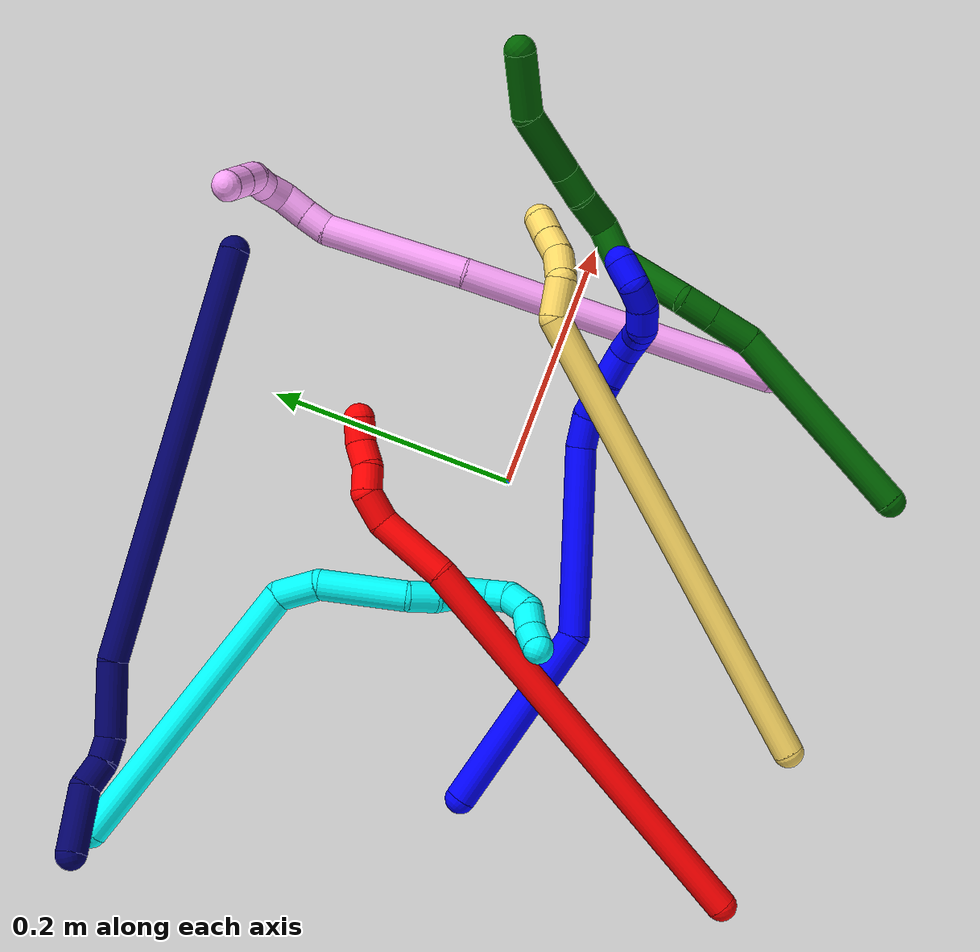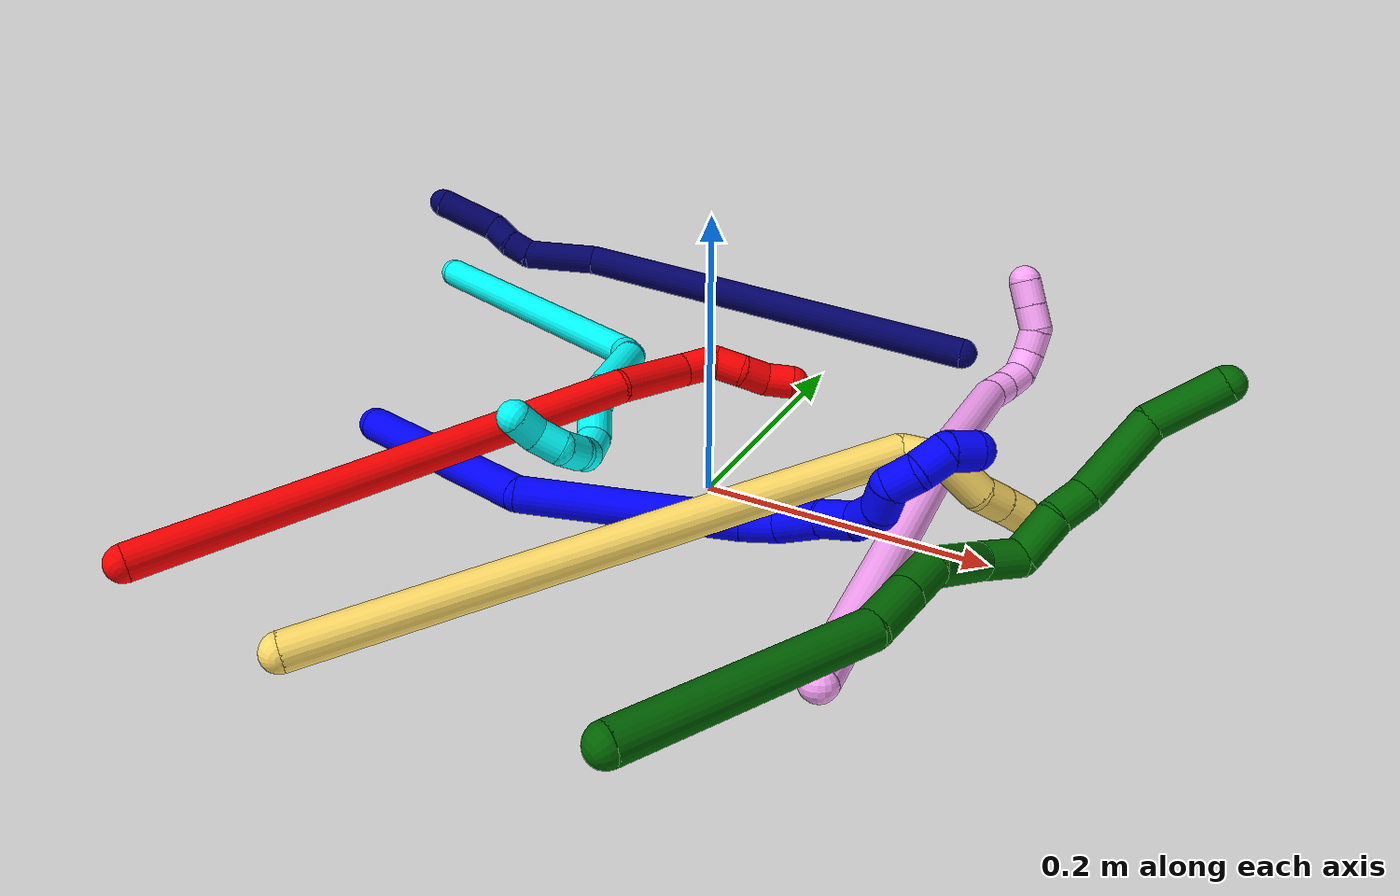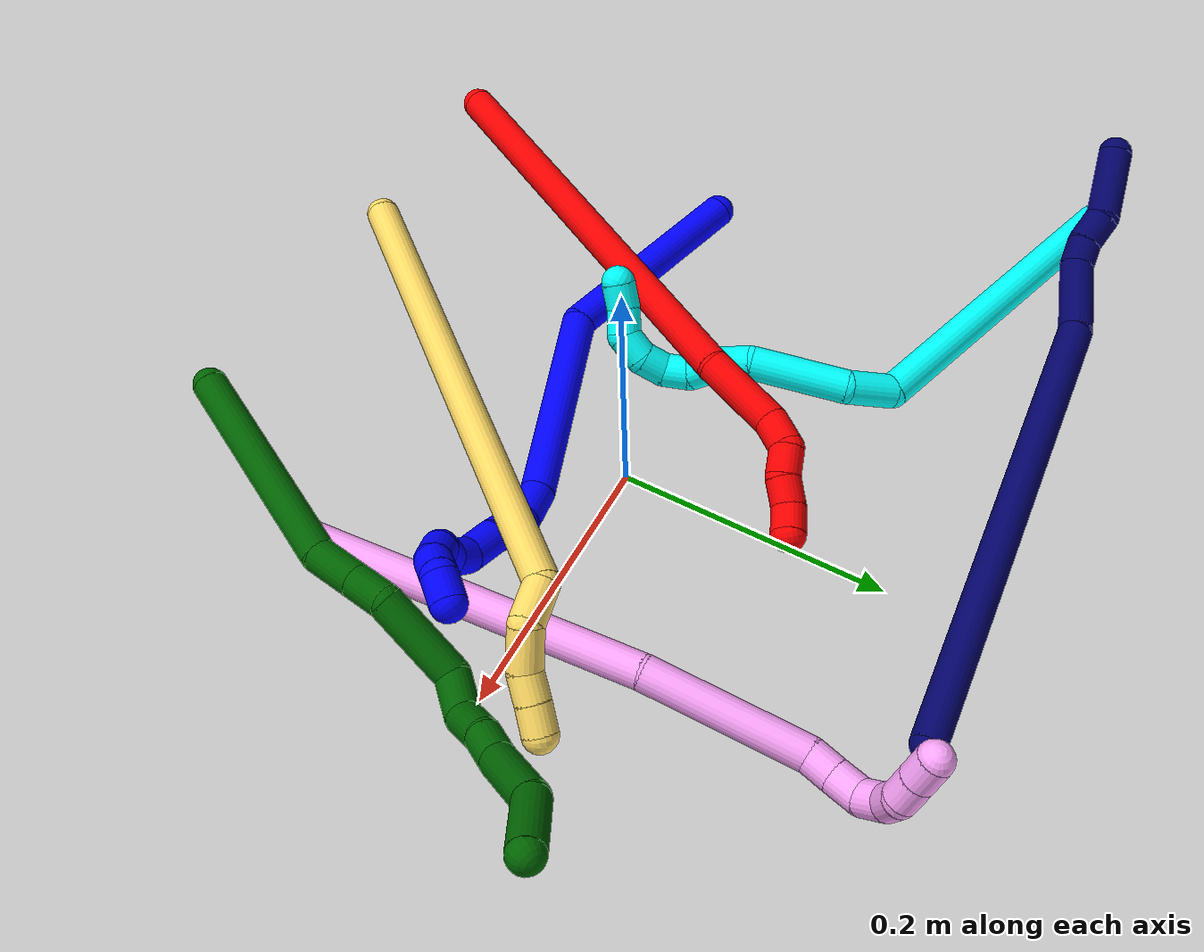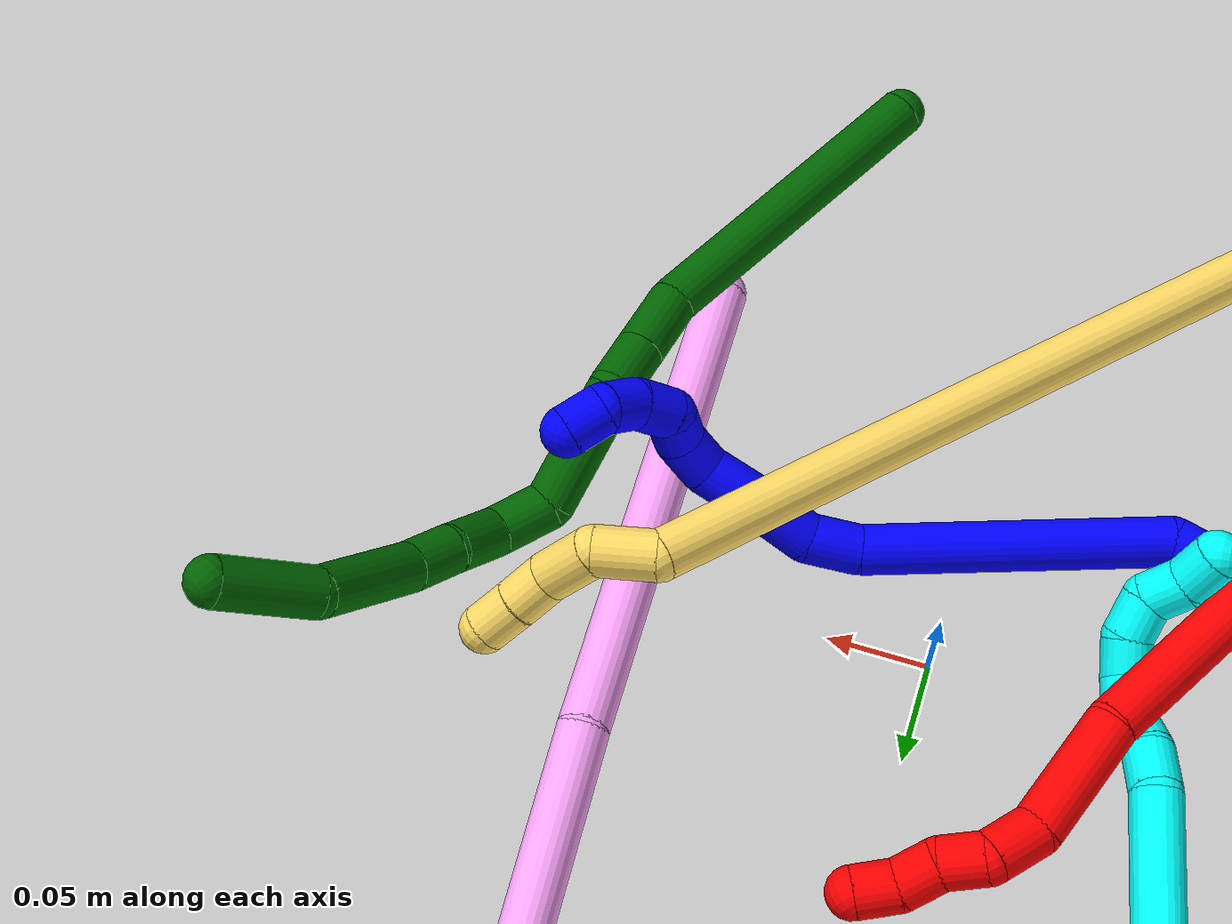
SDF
<sdf version="1.7">
 <world name="default">
  <plugin name="TubeGeneratorPlugin" filename="libtube_generator_plugin.so"/>
  <model name="photoneo_s_sensor">
   <static>1</static>
   <pose>0 0 2 1.57079 1.57079 3.14159</pose>
   <link name="link">
    <inertial><mass>0.1</mass></inertial>
    <sensor name="sensor" type="depth">
     <update_rate>30</update_rate>
     <camera>
      <horizontal_fov>1.22</horizontal_fov>
      <image><width>1920</width><height>1200</height><format>B8G8R8</format></image>
      <clip><near>0.1</near><far>4</far></clip>
      <depth_camera><output>points</output></depth_camera>
     </camera>
     <plugin name="camera_plugin" filename="libgazebo_ros_depth_camera.so">
      <baseline>0.2</baseline>
      <alwaysOn>1</alwaysOn>
      <updateRate>0.0</updateRate>
      <cameraName>camera_ir</cameraName>
      <imageTopicName>/camera/color/image_raw</imageTopicName>
      <cameraInfoTopicName>/camera/color/camera_info</cameraInfoTopicName>
      <depthImageTopicName>/camera/depth/image_raw</depthImageTopicName>
      <depthImageCameraInfoTopicName>/camera/depth/camera_info</depthImageCameraInfoTopicName>
      <pointCloudTopicName>/camera/depth/points</pointCloudTopicName>
      <frameName>fr_optical</frameName>
      <pointCloudCutoff>0.1</pointCloudCutoff>
      <pointCloudCutoffMax>2.0</pointCloudCutoffMax>
      <distortionK1>0</distortionK1>
      <distortionK2>0</distortionK2>
      <distortionK3>0</distortionK3>
      <distortionT1>0</distortionT1>
      <distortionT2>0</distortionT2>
      <CxPrime>0</CxPrime>
      <Cx>0</Cx>
      <Cy>0</Cy>
      <focalLength>0</focalLength>
      <hackBaseline>0</hackBaseline>
     </plugin>
    </sensor>
   </link>
  </model>
  <gravity>0 0 -9.8</gravity>
  <magnetic_field>6e-06 2.3e-05 -4.2e-05</magnetic_field>
  <atmosphere type="adiabatic"/>
  <physics name="default_physics" default="0" type="ode">
   <max_step_size>0.003</max_step_size>
   <real_time_factor>1</real_time_factor>
   <real_time_update_rate>1000</real_time_update_rate>
   <max_contacts>10000</max_contacts>
   <ode>
    <solver>
     <type>quick</type>
     <iters>100</iters>
     <sor>1.3</sor>
     <use_dynamic_moi_rescaling>0</use_dynamic_moi_rescaling>
    </solver>
    <constraints>
     <contact_max_correcting_vel>0</contact_max_correcting_vel>
     <contact_surface_layer>0.001</contact_surface_layer>
     <cfm>0</cfm>
     <erp>0.2</erp>
    </constraints>
   </ode>
  </physics>
  <scene><ambient>0.4 0.4 0.4 1</ambient><background>0.7 0.7 0.7 1</background><shadows>0</shadows></scene>
  <audio><device>default</device></audio>
  <spherical_coordinates>
   <surface_model>EARTH_WGS84</surface_model>
   <latitude_deg>0</latitude_deg>
   <longitude_deg>0</longitude_deg>
   <elevation>0</elevation>
   <heading_deg>0</heading_deg>
  </spherical_coordinates>
  <model name="bin">
   <static>1</static>
   <link name="bottom">
    <collision name="collision-bottom">
     <pose>0 0 -0.01 0 -0 0</pose>
     <geometry><box><size>0.8 0.6 0.02</size></box></geometry>
     <surface>
      <friction><ode><mu>100</mu><mu2>100</mu2></ode></friction>
      <contact><collide_bitmask>65535</collide_bitmask></contact>
     </surface>
    </collision>
   </link>
   <link name="west_wall">
    <collision name="collision-west_wall">
     <pose>-0.41 0 0.1 0 -0 0</pose>
     <geometry><box><size>0.02 0.6 0.2</size></box></geometry>
     <surface>
      <friction><ode><mu>100</mu><mu2>100</mu2></ode></friction>
      <contact><collide_bitmask>65535</collide_bitmask></contact>
     </surface>
    </collision>
   </link>
   <link name="east_wall">
    <collision name="collision-east_wall">
     <pose>0.41 0 0.1 0 -0 0</pose>
     <geometry><box><size>0.02 0.6 0.2</size></box></geometry>
     <surface>
      <friction><ode><mu>100</mu><mu2>100</mu2></ode></friction>
      <contact><collide_bitmask>65535</collide_bitmask></contact>
     </surface>
    </collision>
   </link>
   <link name="south_wall">
    <collision name="collision-south_wall">
     <pose>0 -0.31 0.1 0 -0 0</pose>
     <geometry><box><size>0.8 0.02 0.2</size></box></geometry>
     <surface>
      <friction><ode><mu>100</mu><mu2>100</mu2></ode></friction>
      <contact><collide_bitmask>65535</collide_bitmask></contact>
     </surface>
    </collision>
   </link>
   <link name="north_wall">
    <collision name="collision-north_wall">
     <pose>0 0.31 0.1 0 -0 0</pose>
     <geometry><box><size>0.8 0.02 0.2</size></box></geometry>
     <surface>
      <friction><ode><mu>100</mu><mu2>100</mu2></ode></friction>
      <contact><collide_bitmask>65535</collide_bitmask></contact>
     </surface>
    </collision>
   </link>
  </model>
  <model name="1">
   <static>0</static>
   <link name="1">
    <collision name="collision-cylinder-e_1_1_4">
     <pose>0.017236 0.002004 -0.077901 -3.11587 0.217678 -2.90726</pose>
     <geometry><cylinder><radius>0.0125</radius><length>0.159621</length></cylinder></geometry>
     <surface>
      <friction><ode><mu>1.16</mu><mu2>1.16</mu2><slip1>0</slip1><slip2>0</slip2></ode></friction>
      <contact><ode><kp>1e+06</kp><kd>1</kd><max_vel>0</max_vel><min_depth>0.001</min_depth></ode></contact>
     </surface>
    </collision>
    <visual name="visual-cylinder-e_1_1_4">
     <pose>0.017236 0.002004 -0.077901 -3.11587 0.217678 -2.90726</pose>
     <geometry><cylinder><radius>0.0125</radius><length>0.159621</length></cylinder></geometry>
     <material><ambient>0 0 1 1</ambient></material>
    </visual>
    <collision name="collision-cylinder-e_2_4_5">
     <pose>0.060237 0.044857 -0.214349 -2.53241 0.346358 -1.01555</pose>
     <geometry><cylinder><radius>0.0125</radius><length>0.15179</length></cylinder></geometry>
     <surface>
      <friction><ode><mu>1.16</mu><mu2>1.16</mu2><slip1>0</slip1><slip2>0</slip2></ode></friction>
      <contact><ode><kp>1e+06</kp><kd>1</kd><max_vel>0</max_vel><min_depth>0.001</min_depth></ode></contact>
     </surface>
    </collision>
    <visual name="visual-cylinder-e_2_4_5">
     <pose>0.060237 0.044857 -0.214349 -2.53241 0.346358 -1.01555</pose>
     <geometry><cylinder><radius>0.0125</radius><length>0.15179</length></cylinder></geometry>
     <material><ambient>0 0 1 1</ambient></material>
    </visual>
    <collision name="collision-cylinder-e_3_5_6">
     <pose>0.092342 0.089831 -0.283835 -2.78096 0.496932 -1.89549</pose>
     <geometry><cylinder><radius>0.0125</radius><length>0.026601</length></cylinder></geometry>
     <surface>
      <friction><ode><mu>1.16</mu><mu2>1.16</mu2><slip1>0</slip1><slip2>0</slip2></ode></friction>
      <contact><ode><kp>1e+06</kp><kd>1</kd><max_vel>0</max_vel><min_depth>0.001</min_depth></ode></contact>
     </surface>
    </collision>
    <visual name="visual-cylinder-e_3_5_6">
     <pose>0.092342 0.089831 -0.283835 -2.78096 0.496932 -1.89549</pose>
     <geometry><cylinder><radius>0.0125</radius><length>0.026601</length></cylinder></geometry>
     <material><ambient>0 0 1 1</ambient></material>
    </visual>
    <collision name="collision-cylinder-e_4_6_7">
     <pose>0.109317 0.092621 -0.308574 3.04512 0.654322 2.85898</pose>
     <geometry><cylinder><radius>0.0125</radius><length>0.034946</length></cylinder></geometry>
     <surface>
      <friction><ode><mu>1.16</mu><mu2>1.16</mu2><slip1>0</slip1><slip2>0</slip2></ode></friction>
      <contact><ode><kp>1e+06</kp><kd>1</kd><max_vel>0</max_vel><min_depth>0.001</min_depth></ode></contact>
     </surface>
    </collision>
    <visual name="visual-cylinder-e_4_6_7">
     <pose>0.109317 0.092621 -0.308574 3.04512 0.654322 2.85898</pose>
     <geometry><cylinder><radius>0.0125</radius><length>0.034946</length></cylinder></geometry>
     <material><ambient>0 0 1 1</ambient></material>
    </visual>
    <collision name="collision-cylinder-e_5_7_8">
     <pose>0.126132 0.09102 -0.333576 3.11791 0.504036 3.0497</pose>
     <geometry><cylinder><radius>0.0125</radius><length>0.025593</length></cylinder></geometry>
     <surface>
      <friction><ode><mu>1.16</mu><mu2>1.16</mu2><slip1>0</slip1><slip2>0</slip2></ode></friction>
      <contact><ode><kp>1e+06</kp><kd>1</kd><max_vel>0</max_vel><min_depth>0.001</min_depth></ode></contact>
     </surface>
    </collision>
    <visual name="visual-cylinder-e_5_7_8">
     <pose>0.126132 0.09102 -0.333576 3.11791 0.504036 3.0497</pose>
     <geometry><cylinder><radius>0.0125</radius><length>0.025593</length></cylinder></geometry>
     <material><ambient>0 0 1 1</ambient></material>
    </visual>
    <collision name="collision-cylinder-e_6_8_9">
     <pose>0.139952 0.087854 -0.351361 2.72653 0.815486 2.23444</pose>
     <geometry><cylinder><radius>0.0125</radius><length>0.020986</length></cylinder></geometry>
     <surface>
      <friction><ode><mu>1.16</mu><mu2>1.16</mu2><slip1>0</slip1><slip2>0</slip2></ode></friction>
      <contact><ode><kp>1e+06</kp><kd>1</kd><max_vel>0</max_vel><min_depth>0.001</min_depth></ode></contact>
     </surface>
    </collision>
    <visual name="visual-cylinder-e_6_8_9">
     <pose>0.139952 0.087854 -0.351361 2.72653 0.815486 2.23444</pose>
     <geometry><cylinder><radius>0.0125</radius><length>0.020986</length></cylinder></geometry>
     <material><ambient>0 0 1 1</ambient></material>
    </visual>
    <collision name="collision-cylinder-e_7_9_10">
     <pose>0.15677 0.081054 -0.359055 1.84864 1.15485 1.42433</pose>
     <geometry><cylinder><radius>0.0125</radius><length>0.02007</length></cylinder></geometry>
     <surface>
      <friction><ode><mu>1.16</mu><mu2>1.16</mu2><slip1>0</slip1><slip2>0</slip2></ode></friction>
      <contact><ode><kp>1e+06</kp><kd>1</kd><max_vel>0</max_vel><min_depth>0.001</min_depth></ode></contact>
     </surface>
    </collision>
    <visual name="visual-cylinder-e_7_9_10">
     <pose>0.15677 0.081054 -0.359055 1.84864 1.15485 1.42433</pose>
     <geometry><cylinder><radius>0.0125</radius><length>0.02007</length></cylinder></geometry>
     <material><ambient>0 0 1 1</ambient></material>
    </visual>
    <collision name="collision-cylinder-e_8_10_11">
     <pose>0.174473 0.079323 -0.365291 -2.74133 0.992514 -2.4247</pose>
     <geometry><cylinder><radius>0.0125</radius><length>0.020356</length></cylinder></geometry>
     <surface>
      <friction><ode><mu>1.16</mu><mu2>1.16</mu2><slip1>0</slip1><slip2>0</slip2></ode></friction>
      <contact><ode><kp>1e+06</kp><kd>1</kd><max_vel>0</max_vel><min_depth>0.001</min_depth></ode></contact>
     </surface>
    </collision>
    <visual name="visual-cylinder-e_8_10_11">
     <pose>0.174473 0.079323 -0.365291 -2.74133 0.992514 -2.4247</pose>
     <geometry><cylinder><radius>0.0125</radius><length>0.020356</length></cylinder></geometry>
     <material><ambient>0 0 1 1</ambient></material>
    </visual>
    <collision name="collision-cylinder-e_9_11_12">
     <pose>0.191255 0.086582 -0.372851 -2.01718 0.971278 -1.39467</pose>
     <geometry><cylinder><radius>0.0125</radius><length>0.020007</length></cylinder></geometry>
     <surface>
      <friction><ode><mu>1.16</mu><mu2>1.16</mu2><slip1>0</slip1><slip2>0</slip2></ode></friction>
      <contact><ode><kp>1e+06</kp><kd>1</kd><max_vel>0</max_vel><min_depth>0.001</min_depth></ode></contact>
     </surface>
    </collision>
    <visual name="visual-cylinder-e_9_11_12">
     <pose>0.191255 0.086582 -0.372851 -2.01718 0.971278 -1.39467</pose>
     <geometry><cylinder><radius>0.0125</radius><length>0.020007</length></cylinder></geometry>
     <material><ambient>0 0 1 1</ambient></material>
    </visual>
    <collision name="collision-cylinder-e_10_12_2">
     <pose>0.202468 0.100505 -0.378971 -1.96585 0.299445 -0.445182</pose>
     <geometry><cylinder><radius>0.0125</radius><length>0.02003</length></cylinder></geometry>
     <surface>
      <friction><ode><mu>1.16</mu><mu2>1.16</mu2><slip1>0</slip1><slip2>0</slip2></ode></friction>
      <contact><ode><kp>1e+06</kp><kd>1</kd><max_vel>0</max_vel><min_depth>0.001</min_depth></ode></contact>
     </surface>
    </collision>
    <visual name="visual-cylinder-e_10_12_2">
     <pose>0.202468 0.100505 -0.378971 -1.96585 0.299445 -0.445182</pose>
     <geometry><cylinder><radius>0.0125</radius><length>0.02003</length></cylinder></geometry>
     <material><ambient>0 0 1 1</ambient></material>
    </visual>
    <collision name="collision-sphere-2">
     <pose>0.205422 0.109338 -0.382653 0 -0 0</pose>
     <geometry><sphere><radius>0.0125</radius></sphere></geometry>
     <surface>
      <friction><ode><mu>1.16</mu><mu2>1.16</mu2><slip1>0</slip1><slip2>0</slip2></ode></friction>
      <contact><ode><kp>1e+06</kp><kd>1</kd><max_vel>0</max_vel><min_depth>0.001</min_depth></ode></contact>
     </surface>
    </collision>
    <visual name="visual-sphere-2">
     <pose>0.205422 0.109338 -0.382653 0 -0 0</pose>
     <geometry><sphere><radius>0.0125</radius></sphere></geometry>
     <material><ambient>0 0 1 1</ambient></material>
    </visual>
    <collision name="collision-sphere-12">
     <pose>0.199514 0.091673 -0.375288 0 -0 0</pose>
     <geometry><sphere><radius>0.0125</radius></sphere></geometry>
     <surface>
      <friction><ode><mu>1.16</mu><mu2>1.16</mu2><slip1>0</slip1><slip2>0</slip2></ode></friction>
      <contact><ode><kp>1e+06</kp><kd>1</kd><max_vel>0</max_vel><min_depth>0.001</min_depth></ode></contact>
     </surface>
    </collision>
    <visual name="visual-sphere-12">
     <pose>0.199514 0.091673 -0.375288 0 -0 0</pose>
     <geometry><sphere><radius>0.0125</radius></sphere></geometry>
     <material><ambient>0 0 1 1</ambient></material>
    </visual>
    <collision name="collision-sphere-11">
     <pose>0.182996 0.08149 -0.370414 0 -0 0</pose>
     <geometry><sphere><radius>0.0125</radius></sphere></geometry>
     <surface>
      <friction><ode><mu>1.16</mu><mu2>1.16</mu2><slip1>0</slip1><slip2>0</slip2></ode></friction>
      <contact><ode><kp>1e+06</kp><kd>1</kd><max_vel>0</max_vel><min_depth>0.001</min_depth></ode></contact>
     </surface>
    </collision>
    <visual name="visual-sphere-11">
     <pose>0.182996 0.08149 -0.370414 0 -0 0</pose>
     <geometry><sphere><radius>0.0125</radius></sphere></geometry>
     <material><ambient>0 0 1 1</ambient></material>
    </visual>
    <collision name="collision-sphere-10">
     <pose>0.16595 0.077155 -0.360167 0 -0 0</pose>
     <geometry><sphere><radius>0.0125</radius></sphere></geometry>
     <surface>
      <friction><ode><mu>1.16</mu><mu2>1.16</mu2><slip1>0</slip1><slip2>0</slip2></ode></friction>
      <contact><ode><kp>1e+06</kp><kd>1</kd><max_vel>0</max_vel><min_depth>0.001</min_depth></ode></contact>
     </surface>
    </collision>
    <visual name="visual-sphere-10">
     <pose>0.16595 0.077155 -0.360167 0 -0 0</pose>
     <geometry><sphere><radius>0.0125</radius></sphere></geometry>
     <material><ambient>0 0 1 1</ambient></material>
    </visual>
    <collision name="collision-sphere-9">
     <pose>0.147591 0.084953 -0.357943 0 -0 0</pose>
     <geometry><sphere><radius>0.0125</radius></sphere></geometry>
     <surface>
      <friction><ode><mu>1.16</mu><mu2>1.16</mu2><slip1>0</slip1><slip2>0</slip2></ode></friction>
      <contact><ode><kp>1e+06</kp><kd>1</kd><max_vel>0</max_vel><min_depth>0.001</min_depth></ode></contact>
     </surface>
    </collision>
    <visual name="visual-sphere-9">
     <pose>0.147591 0.084953 -0.357943 0 -0 0</pose>
     <geometry><sphere><radius>0.0125</radius></sphere></geometry>
     <material><ambient>0 0 1 1</ambient></material>
    </visual>
    <collision name="collision-sphere-4">
     <pose>0.034472 0.004008 -0.155803 0 -0 0</pose>
     <geometry><sphere><radius>0.0125</radius></sphere></geometry>
     <surface>
      <friction><ode><mu>1.16</mu><mu2>1.16</mu2><slip1>0</slip1><slip2>0</slip2></ode></friction>
      <contact><ode><kp>1e+06</kp><kd>1</kd><max_vel>0</max_vel><min_depth>0.001</min_depth></ode></contact>
     </surface>
    </collision>
    <visual name="visual-sphere-4">
     <pose>0.034472 0.004008 -0.155803 0 -0 0</pose>
     <geometry><sphere><radius>0.0125</radius></sphere></geometry>
     <material><ambient>0 0 1 1</ambient></material>
    </visual>
    <collision name="collision-sphere-1">
     <geometry><sphere><radius>0.0125</radius></sphere></geometry>
     <surface>
      <friction><ode><mu>1.16</mu><mu2>1.16</mu2><slip1>0</slip1><slip2>0</slip2></ode></friction>
      <contact><ode><kp>1e+06</kp><kd>1</kd><max_vel>0</max_vel><min_depth>0.001</min_depth></ode></contact>
     </surface>
    </collision>
    <visual name="visual-sphere-1">
     <geometry><sphere><radius>0.0125</radius></sphere></geometry>
     <material><ambient>0 0 1 1</ambient></material>
    </visual>
    <collision name="collision-sphere-8">
     <pose>0.132312 0.090755 -0.344778 0 -0 0</pose>
     <geometry><sphere><radius>0.0125</radius></sphere></geometry>
     <surface>
      <friction><ode><mu>1.16</mu><mu2>1.16</mu2><slip1>0</slip1><slip2>0</slip2></ode></friction>
      <contact><ode><kp>1e+06</kp><kd>1</kd><max_vel>0</max_vel><min_depth>0.001</min_depth></ode></contact>
     </surface>
    </collision>
    <visual name="visual-sphere-8">
     <pose>0.132312 0.090755 -0.344778 0 -0 0</pose>
     <geometry><sphere><radius>0.0125</radius></sphere></geometry>
     <material><ambient>0 0 1 1</ambient></material>
    </visual>
    <collision name="collision-sphere-5">
     <pose>0.086001 0.085705 -0.272895 0 -0 0</pose>
     <geometry><sphere><radius>0.0125</radius></sphere></geometry>
     <surface>
      <friction><ode><mu>1.16</mu><mu2>1.16</mu2><slip1>0</slip1><slip2>0</slip2></ode></friction>
      <contact><ode><kp>1e+06</kp><kd>1</kd><max_vel>0</max_vel><min_depth>0.001</min_depth></ode></contact>
     </surface>
    </collision>
    <visual name="visual-sphere-5">
     <pose>0.086001 0.085705 -0.272895 0 -0 0</pose>
     <geometry><sphere><radius>0.0125</radius></sphere></geometry>
     <material><ambient>0 0 1 1</ambient></material>
    </visual>
    <collision name="collision-sphere-6">
     <pose>0.098682 0.093956 -0.294775 0 -0 0</pose>
     <geometry><sphere><radius>0.0125</radius></sphere></geometry>
     <surface>
      <friction><ode><mu>1.16</mu><mu2>1.16</mu2><slip1>0</slip1><slip2>0</slip2></ode></friction>
      <contact><ode><kp>1e+06</kp><kd>1</kd><max_vel>0</max_vel><min_depth>0.001</min_depth></ode></contact>
     </surface>
    </collision>
    <visual name="visual-sphere-6">
     <pose>0.098682 0.093956 -0.294775 0 -0 0</pose>
     <geometry><sphere><radius>0.0125</radius></sphere></geometry>
     <material><ambient>0 0 1 1</ambient></material>
    </visual>
    <collision name="collision-sphere-7">
     <pose>0.119951 0.091285 -0.322374 0 -0 0</pose>
     <geometry><sphere><radius>0.0125</radius></sphere></geometry>
     <surface>
      <friction><ode><mu>1.16</mu><mu2>1.16</mu2><slip1>0</slip1><slip2>0</slip2></ode></friction>
      <contact><ode><kp>1e+06</kp><kd>1</kd><max_vel>0</max_vel><min_depth>0.001</min_depth></ode></contact>
     </surface>
    </collision>
    <visual name="visual-sphere-7">
     <pose>0.119951 0.091285 -0.322374 0 -0 0</pose>
     <geometry><sphere><radius>0.0125</radius></sphere></geometry>
     <material><ambient>0 0 1 1</ambient></material>
    </visual>
    <inertial>
     <pose>0.077832 0.04783 -0.217816 0 -0 0</pose>
     <mass>0.5</mass>
     <inertia>
      <ixx>-0.000488</ixx>
      <ixy>0</ixy>
      <ixz>0</ixz>
      <iyy>-3.9e-05</iyy>
      <iyz>0</iyz>
      <izz>-0.000387</izz>
     </inertia>
    </inertial>
   </link>
   <pose>-0.251462 -0.054768 0.011497 -1.23347 -1.10526 0.906471</pose>
  </model>
  <model name="2">
   <static>0</static>
   <link name="2">
    <collision name="collision-cylinder-e_1_1_4">
     <pose>-0.074435 0.147826 0.055371 -1.2124 -0.440621 0.308054</pose>
     <geometry><cylinder><radius>0.0125</radius><length>0.349051</length></cylinder></geometry>
     <surface>
      <friction><ode><mu>1.16</mu><mu2>1.16</mu2><slip1>0</slip1><slip2>0</slip2></ode></friction>
      <contact><ode><kp>1e+06</kp><kd>1</kd><max_vel>0</max_vel><min_depth>0.001</min_depth></ode></contact>
     </surface>
    </collision>
    <visual name="visual-cylinder-e_1_1_4">
     <pose>-0.074435 0.147826 0.055371 -1.2124 -0.440621 0.308054</pose>
     <geometry><cylinder><radius>0.0125</radius><length>0.349051</length></cylinder></geometry>
     <material><ambient>1 0 0 1</ambient></material>
    </visual>
    <collision name="collision-cylinder-e_2_4_5">
     <pose>-0.165278 0.316811 0.125095 -0.974781 -0.570533 0.308416</pose>
     <geometry><cylinder><radius>0.0125</radius><length>0.060759</length></cylinder></geometry>
     <surface>
      <friction><ode><mu>1.16</mu><mu2>1.16</mu2><slip1>0</slip1><slip2>0</slip2></ode></friction>
      <contact><ode><kp>1e+06</kp><kd>1</kd><max_vel>0</max_vel><min_depth>0.001</min_depth></ode></contact>
     </surface>
    </collision>
    <visual name="visual-cylinder-e_2_4_5">
     <pose>-0.165278 0.316811 0.125095 -0.974781 -0.570533 0.308416</pose>
     <geometry><cylinder><radius>0.0125</radius><length>0.060759</length></cylinder></geometry>
     <material><ambient>1 0 0 1</ambient></material>
    </visual>
    <collision name="collision-cylinder-e_3_5_6">
     <pose>-0.187606 0.349729 0.141307 -1.41392 -0.461476 0.396106</pose>
     <geometry><cylinder><radius>0.0125</radius><length>0.026592</length></cylinder></geometry>
     <surface>
      <friction><ode><mu>1.16</mu><mu2>1.16</mu2><slip1>0</slip1><slip2>0</slip2></ode></friction>
      <contact><ode><kp>1e+06</kp><kd>1</kd><max_vel>0</max_vel><min_depth>0.001</min_depth></ode></contact>
     </surface>
    </collision>
    <visual name="visual-cylinder-e_3_5_6">
     <pose>-0.187606 0.349729 0.141307 -1.41392 -0.461476 0.396106</pose>
     <geometry><cylinder><radius>0.0125</radius><length>0.026592</length></cylinder></geometry>
     <material><ambient>1 0 0 1</ambient></material>
    </visual>
    <collision name="collision-cylinder-e_4_6_7">
     <pose>-0.201305 0.367821 0.139267 -2.12284 -0.807905 1.30646</pose>
     <geometry><cylinder><radius>0.0125</radius><length>0.021525</length></cylinder></geometry>
     <surface>
      <friction><ode><mu>1.16</mu><mu2>1.16</mu2><slip1>0</slip1><slip2>0</slip2></ode></friction>
      <contact><ode><kp>1e+06</kp><kd>1</kd><max_vel>0</max_vel><min_depth>0.001</min_depth></ode></contact>
     </surface>
    </collision>
    <visual name="visual-cylinder-e_4_6_7">
     <pose>-0.201305 0.367821 0.139267 -2.12284 -0.807905 1.30646</pose>
     <geometry><cylinder><radius>0.0125</radius><length>0.021525</length></cylinder></geometry>
     <material><ambient>1 0 0 1</ambient></material>
    </visual>
    <collision name="collision-cylinder-e_5_7_8">
     <pose>-0.217928 0.379831 0.135124 -1.61357 -0.999604 1.03601</pose>
     <geometry><cylinder><radius>0.0125</radius><length>0.021024</length></cylinder></geometry>
     <surface>
      <friction><ode><mu>1.16</mu><mu2>1.16</mu2><slip1>0</slip1><slip2>0</slip2></ode></friction>
      <contact><ode><kp>1e+06</kp><kd>1</kd><max_vel>0</max_vel><min_depth>0.001</min_depth></ode></contact>
     </surface>
    </collision>
    <visual name="visual-cylinder-e_5_7_8">
     <pose>-0.217928 0.379831 0.135124 -1.61357 -0.999604 1.03601</pose>
     <geometry><cylinder><radius>0.0125</radius><length>0.021024</length></cylinder></geometry>
     <material><ambient>1 0 0 1</ambient></material>
    </visual>
    <collision name="collision-cylinder-e_6_8_2">
     <pose>-0.233135 0.393361 0.131944 -1.92869 -0.649242 0.903396</pose>
     <geometry><cylinder><radius>0.0125</radius><length>0.021049</length></cylinder></geometry>
     <surface>
      <friction><ode><mu>1.16</mu><mu2>1.16</mu2><slip1>0</slip1><slip2>0</slip2></ode></friction>
      <contact><ode><kp>1e+06</kp><kd>1</kd><max_vel>0</max_vel><min_depth>0.001</min_depth></ode></contact>
     </surface>
    </collision>
    <visual name="visual-cylinder-e_6_8_2">
     <pose>-0.233135 0.393361 0.131944 -1.92869 -0.649242 0.903396</pose>
     <geometry><cylinder><radius>0.0125</radius><length>0.021049</length></cylinder></geometry>
     <material><ambient>1 0 0 1</ambient></material>
    </visual>
    <collision name="collision-sphere-2">
     <pose>-0.239498 0.401213 0.129007 0 -0 0</pose>
     <geometry><sphere><radius>0.0125</radius></sphere></geometry>
     <surface>
      <friction><ode><mu>1.16</mu><mu2>1.16</mu2><slip1>0</slip1><slip2>0</slip2></ode></friction>
      <contact><ode><kp>1e+06</kp><kd>1</kd><max_vel>0</max_vel><min_depth>0.001</min_depth></ode></contact>
     </surface>
    </collision>
    <visual name="visual-sphere-2">
     <pose>-0.239498 0.401213 0.129007 0 -0 0</pose>
     <geometry><sphere><radius>0.0125</radius></sphere></geometry>
     <material><ambient>1 0 0 1</ambient></material>
    </visual>
    <collision name="collision-sphere-4">
     <pose>-0.148871 0.295652 0.110742 0 -0 0</pose>
     <geometry><sphere><radius>0.0125</radius></sphere></geometry>
     <surface>
      <friction><ode><mu>1.16</mu><mu2>1.16</mu2><slip1>0</slip1><slip2>0</slip2></ode></friction>
      <contact><ode><kp>1e+06</kp><kd>1</kd><max_vel>0</max_vel><min_depth>0.001</min_depth></ode></contact>
     </surface>
    </collision>
    <visual name="visual-sphere-4">
     <pose>-0.148871 0.295652 0.110742 0 -0 0</pose>
     <geometry><sphere><radius>0.0125</radius></sphere></geometry>
     <material><ambient>1 0 0 1</ambient></material>
    </visual>
    <collision name="collision-sphere-1">
     <geometry><sphere><radius>0.0125</radius></sphere></geometry>
     <surface>
      <friction><ode><mu>1.16</mu><mu2>1.16</mu2><slip1>0</slip1><slip2>0</slip2></ode></friction>
      <contact><ode><kp>1e+06</kp><kd>1</kd><max_vel>0</max_vel><min_depth>0.001</min_depth></ode></contact>
     </surface>
    </collision>
    <visual name="visual-sphere-1">
     <geometry><sphere><radius>0.0125</radius></sphere></geometry>
     <material><ambient>1 0 0 1</ambient></material>
    </visual>
    <collision name="collision-sphere-8">
     <pose>-0.226772 0.385509 0.134881 0 -0 0</pose>
     <geometry><sphere><radius>0.0125</radius></sphere></geometry>
     <surface>
      <friction><ode><mu>1.16</mu><mu2>1.16</mu2><slip1>0</slip1><slip2>0</slip2></ode></friction>
      <contact><ode><kp>1e+06</kp><kd>1</kd><max_vel>0</max_vel><min_depth>0.001</min_depth></ode></contact>
     </surface>
    </collision>
    <visual name="visual-sphere-8">
     <pose>-0.226772 0.385509 0.134881 0 -0 0</pose>
     <geometry><sphere><radius>0.0125</radius></sphere></geometry>
     <material><ambient>1 0 0 1</ambient></material>
    </visual>
    <collision name="collision-sphere-5">
     <pose>-0.181685 0.33797 0.139447 0 -0 0</pose>
     <geometry><sphere><radius>0.0125</radius></sphere></geometry>
     <surface>
      <friction><ode><mu>1.16</mu><mu2>1.16</mu2><slip1>0</slip1><slip2>0</slip2></ode></friction>
      <contact><ode><kp>1e+06</kp><kd>1</kd><max_vel>0</max_vel><min_depth>0.001</min_depth></ode></contact>
     </surface>
    </collision>
    <visual name="visual-sphere-5">
     <pose>-0.181685 0.33797 0.139447 0 -0 0</pose>
     <geometry><sphere><radius>0.0125</radius></sphere></geometry>
     <material><ambient>1 0 0 1</ambient></material>
    </visual>
    <collision name="collision-sphere-6">
     <pose>-0.193526 0.361488 0.143167 0 -0 0</pose>
     <geometry><sphere><radius>0.0125</radius></sphere></geometry>
     <surface>
      <friction><ode><mu>1.16</mu><mu2>1.16</mu2><slip1>0</slip1><slip2>0</slip2></ode></friction>
      <contact><ode><kp>1e+06</kp><kd>1</kd><max_vel>0</max_vel><min_depth>0.001</min_depth></ode></contact>
     </surface>
    </collision>
    <visual name="visual-sphere-6">
     <pose>-0.193526 0.361488 0.143167 0 -0 0</pose>
     <geometry><sphere><radius>0.0125</radius></sphere></geometry>
     <material><ambient>1 0 0 1</ambient></material>
    </visual>
    <collision name="collision-sphere-7">
     <pose>-0.209085 0.374153 0.135367 0 -0 0</pose>
     <geometry><sphere><radius>0.0125</radius></sphere></geometry>
     <surface>
      <friction><ode><mu>1.16</mu><mu2>1.16</mu2><slip1>0</slip1><slip2>0</slip2></ode></friction>
      <contact><ode><kp>1e+06</kp><kd>1</kd><max_vel>0</max_vel><min_depth>0.001</min_depth></ode></contact>
     </surface>
    </collision>
    <visual name="visual-sphere-7">
     <pose>-0.209085 0.374153 0.135367 0 -0 0</pose>
     <geometry><sphere><radius>0.0125</radius></sphere></geometry>
     <material><ambient>1 0 0 1</ambient></material>
    </visual>
    <inertial>
     <pose>-0.10967 0.208662 0.078603 0 -0 0</pose>
     <mass>0.5</mass>
     <inertia>
      <ixx>0.004053</ixx>
      <ixy>0</ixy>
      <ixz>0</ixz>
      <iyy>0.002653</iyy>
      <iyz>0</iyz>
      <izz>-0.00149</izz>
     </inertia>
    </inertial>
   </link>
   <pose>-0.255935 -0.279669 0.023231 1.6596 -1.01049 -2.48476</pose>
  </model>
  <model name="3">
   <static>0</static>
   <link name="3">
    <collision name="collision-cylinder-e_1_1_4">
     <pose>0.018949 -0.042752 -0.111891 2.77663 0.1569 0.805422</pose>
     <geometry><cylinder><radius>0.0125</radius><length>0.242539</length></cylinder></geometry>
     <surface>
      <friction><ode><mu>1.16</mu><mu2>1.16</mu2><slip1>0</slip1><slip2>0</slip2></ode></friction>
      <contact><ode><kp>1e+06</kp><kd>1</kd><max_vel>0</max_vel><min_depth>0.001</min_depth></ode></contact>
     </surface>
    </collision>
    <visual name="visual-cylinder-e_1_1_4">
     <pose>0.018949 -0.042752 -0.111891 2.77663 0.1569 0.805422</pose>
     <geometry><cylinder><radius>0.0125</radius><length>0.242539</length></cylinder></geometry>
     <material><ambient>0.003922 1 0.996078 1</ambient></material>
    </visual>
    <collision name="collision-cylinder-e_2_4_5">
     <pose>0.041914 -0.101374 -0.232384 2.0675 0.218868 0.364953</pose>
     <geometry><cylinder><radius>0.0125</radius><length>0.036987</length></cylinder></geometry>
     <surface>
      <friction><ode><mu>1.16</mu><mu2>1.16</mu2><slip1>0</slip1><slip2>0</slip2></ode></friction>
      <contact><ode><kp>1e+06</kp><kd>1</kd><max_vel>0</max_vel><min_depth>0.001</min_depth></ode></contact>
     </surface>
    </collision>
    <visual name="visual-cylinder-e_2_4_5">
     <pose>0.041914 -0.101374 -0.232384 2.0675 0.218868 0.364953</pose>
     <geometry><cylinder><radius>0.0125</radius><length>0.036987</length></cylinder></geometry>
     <material><ambient>0.003922 1 0.996078 1</ambient></material>
    </visual>
    <collision name="collision-cylinder-e_3_5_6">
     <pose>0.039726 -0.151547 -0.248789 1.79447 -0.174535 -0.218382</pose>
     <geometry><cylinder><radius>0.0125</radius><length>0.071442</length></cylinder></geometry>
     <surface>
      <friction><ode><mu>1.16</mu><mu2>1.16</mu2><slip1>0</slip1><slip2>0</slip2></ode></friction>
      <contact><ode><kp>1e+06</kp><kd>1</kd><max_vel>0</max_vel><min_depth>0.001</min_depth></ode></contact>
     </surface>
    </collision>
    <visual name="visual-cylinder-e_3_5_6">
     <pose>0.039726 -0.151547 -0.248789 1.79447 -0.174535 -0.218382</pose>
     <geometry><cylinder><radius>0.0125</radius><length>0.071442</length></cylinder></geometry>
     <material><ambient>0.003922 1 0.996078 1</ambient></material>
    </visual>
    <collision name="collision-cylinder-e_4_6_7">
     <pose>0.028199 -0.195252 -0.260893 1.9998 -0.475509 -0.721635</pose>
     <geometry><cylinder><radius>0.0125</radius><length>0.023262</length></cylinder></geometry>
     <surface>
      <friction><ode><mu>1.16</mu><mu2>1.16</mu2><slip1>0</slip1><slip2>0</slip2></ode></friction>
      <contact><ode><kp>1e+06</kp><kd>1</kd><max_vel>0</max_vel><min_depth>0.001</min_depth></ode></contact>
     </surface>
    </collision>
    <visual name="visual-cylinder-e_4_6_7">
     <pose>0.028199 -0.195252 -0.260893 1.9998 -0.475509 -0.721635</pose>
     <geometry><cylinder><radius>0.0125</radius><length>0.023262</length></cylinder></geometry>
     <material><ambient>0.003922 1 0.996078 1</ambient></material>
    </visual>
    <collision name="collision-cylinder-e_5_7_8">
     <pose>0.016056 -0.212527 -0.272218 2.29933 -0.573819 -1.16493</pose>
     <geometry><cylinder><radius>0.0125</radius><length>0.025121</length></cylinder></geometry>
     <surface>
      <friction><ode><mu>1.16</mu><mu2>1.16</mu2><slip1>0</slip1><slip2>0</slip2></ode></friction>
      <contact><ode><kp>1e+06</kp><kd>1</kd><max_vel>0</max_vel><min_depth>0.001</min_depth></ode></contact>
     </surface>
    </collision>
    <visual name="visual-cylinder-e_5_7_8">
     <pose>0.016056 -0.212527 -0.272218 2.29933 -0.573819 -1.16493</pose>
     <geometry><cylinder><radius>0.0125</radius><length>0.025121</length></cylinder></geometry>
     <material><ambient>0.003922 1 0.996078 1</ambient></material>
    </visual>
    <collision name="collision-cylinder-e_6_8_9">
     <pose>0.006179 -0.229511 -0.282061 1.87097 -0.310225 -0.417981</pose>
     <geometry><cylinder><radius>0.0125</radius><length>0.020036</length></cylinder></geometry>
     <surface>
      <friction><ode><mu>1.16</mu><mu2>1.16</mu2><slip1>0</slip1><slip2>0</slip2></ode></friction>
      <contact><ode><kp>1e+06</kp><kd>1</kd><max_vel>0</max_vel><min_depth>0.001</min_depth></ode></contact>
     </surface>
    </collision>
    <visual name="visual-cylinder-e_6_8_9">
     <pose>0.006179 -0.229511 -0.282061 1.87097 -0.310225 -0.417981</pose>
     <geometry><cylinder><radius>0.0125</radius><length>0.020036</length></cylinder></geometry>
     <material><ambient>0.003922 1 0.996078 1</ambient></material>
    </visual>
    <collision name="collision-cylinder-e_7_9_10">
     <pose>0.00601 -0.248278 -0.285973 1.68334 0.289002 0.322939</pose>
     <geometry><cylinder><radius>0.0125</radius><length>0.020272</length></cylinder></geometry>
     <surface>
      <friction><ode><mu>1.16</mu><mu2>1.16</mu2><slip1>0</slip1><slip2>0</slip2></ode></friction>
      <contact><ode><kp>1e+06</kp><kd>1</kd><max_vel>0</max_vel><min_depth>0.001</min_depth></ode></contact>
     </surface>
    </collision>
    <visual name="visual-cylinder-e_7_9_10">
     <pose>0.00601 -0.248278 -0.285973 1.68334 0.289002 0.322939</pose>
     <geometry><cylinder><radius>0.0125</radius><length>0.020272</length></cylinder></geometry>
     <material><ambient>0.003922 1 0.996078 1</ambient></material>
    </visual>
    <collision name="collision-cylinder-e_8_10_11">
     <pose>0.011025 -0.267317 -0.28377 1.2332 0.2106 0.149545</pose>
     <geometry><cylinder><radius>0.0125</radius><length>0.020342</length></cylinder></geometry>
     <surface>
      <friction><ode><mu>1.16</mu><mu2>1.16</mu2><slip1>0</slip1><slip2>0</slip2></ode></friction>
      <contact><ode><kp>1e+06</kp><kd>1</kd><max_vel>0</max_vel><min_depth>0.001</min_depth></ode></contact>
     </surface>
    </collision>
    <visual name="visual-cylinder-e_8_10_11">
     <pose>0.011025 -0.267317 -0.28377 1.2332 0.2106 0.149545</pose>
     <geometry><cylinder><radius>0.0125</radius><length>0.020342</length></cylinder></geometry>
     <material><ambient>0.003922 1 0.996078 1</ambient></material>
    </visual>
    <collision name="collision-cylinder-e_9_11_12">
     <pose>0.014802 -0.281755 -0.272005 0.537923 0.165824 0.045805</pose>
     <geometry><cylinder><radius>0.0125</radius><length>0.02</length></cylinder></geometry>
     <surface>
      <friction><ode><mu>1.16</mu><mu2>1.16</mu2><slip1>0</slip1><slip2>0</slip2></ode></friction>
      <contact><ode><kp>1e+06</kp><kd>1</kd><max_vel>0</max_vel><min_depth>0.001</min_depth></ode></contact>
     </surface>
    </collision>
    <visual name="visual-cylinder-e_9_11_12">
     <pose>0.014802 -0.281755 -0.272005 0.537923 0.165824 0.045805</pose>
     <geometry><cylinder><radius>0.0125</radius><length>0.02</length></cylinder></geometry>
     <material><ambient>0.003922 1 0.996078 1</ambient></material>
    </visual>
    <collision name="collision-cylinder-e_10_12_2">
     <pose>0.020629 -0.2932 -0.257078 0.780242 0.430861 0.179478</pose>
     <geometry><cylinder><radius>0.0125</radius><length>0.02</length></cylinder></geometry>
     <surface>
      <friction><ode><mu>1.16</mu><mu2>1.16</mu2><slip1>0</slip1><slip2>0</slip2></ode></friction>
      <contact><ode><kp>1e+06</kp><kd>1</kd><max_vel>0</max_vel><min_depth>0.001</min_depth></ode></contact>
     </surface>
    </collision>
    <visual name="visual-cylinder-e_10_12_2">
     <pose>0.020629 -0.2932 -0.257078 0.780242 0.430861 0.179478</pose>
     <geometry><cylinder><radius>0.0125</radius><length>0.02</length></cylinder></geometry>
     <material><ambient>0.003922 1 0.996078 1</ambient></material>
    </visual>
    <collision name="collision-sphere-2">
     <pose>0.024806 -0.299592 -0.25062 0 -0 0</pose>
     <geometry><sphere><radius>0.0125</radius></sphere></geometry>
     <surface>
      <friction><ode><mu>1.16</mu><mu2>1.16</mu2><slip1>0</slip1><slip2>0</slip2></ode></friction>
      <contact><ode><kp>1e+06</kp><kd>1</kd><max_vel>0</max_vel><min_depth>0.001</min_depth></ode></contact>
     </surface>
    </collision>
    <visual name="visual-sphere-2">
     <pose>0.024806 -0.299592 -0.25062 0 -0 0</pose>
     <geometry><sphere><radius>0.0125</radius></sphere></geometry>
     <material><ambient>0.003922 1 0.996078 1</ambient></material>
    </visual>
    <collision name="collision-sphere-12">
     <pose>0.016452 -0.286808 -0.263535 0 -0 0</pose>
     <geometry><sphere><radius>0.0125</radius></sphere></geometry>
     <surface>
      <friction><ode><mu>1.16</mu><mu2>1.16</mu2><slip1>0</slip1><slip2>0</slip2></ode></friction>
      <contact><ode><kp>1e+06</kp><kd>1</kd><max_vel>0</max_vel><min_depth>0.001</min_depth></ode></contact>
     </surface>
    </collision>
    <visual name="visual-sphere-12">
     <pose>0.016452 -0.286808 -0.263535 0 -0 0</pose>
     <geometry><sphere><radius>0.0125</radius></sphere></geometry>
     <material><ambient>0.003922 1 0.996078 1</ambient></material>
    </visual>
    <collision name="collision-sphere-11">
     <pose>0.013151 -0.276702 -0.280475 0 -0 0</pose>
     <geometry><sphere><radius>0.0125</radius></sphere></geometry>
     <surface>
      <friction><ode><mu>1.16</mu><mu2>1.16</mu2><slip1>0</slip1><slip2>0</slip2></ode></friction>
      <contact><ode><kp>1e+06</kp><kd>1</kd><max_vel>0</max_vel><min_depth>0.001</min_depth></ode></contact>
     </surface>
    </collision>
    <visual name="visual-sphere-11">
     <pose>0.013151 -0.276702 -0.280475 0 -0 0</pose>
     <geometry><sphere><radius>0.0125</radius></sphere></geometry>
     <material><ambient>0.003922 1 0.996078 1</ambient></material>
    </visual>
    <collision name="collision-sphere-10">
     <pose>0.008899 -0.257932 -0.287064 0 -0 0</pose>
     <geometry><sphere><radius>0.0125</radius></sphere></geometry>
     <surface>
      <friction><ode><mu>1.16</mu><mu2>1.16</mu2><slip1>0</slip1><slip2>0</slip2></ode></friction>
      <contact><ode><kp>1e+06</kp><kd>1</kd><max_vel>0</max_vel><min_depth>0.001</min_depth></ode></contact>
     </surface>
    </collision>
    <visual name="visual-sphere-10">
     <pose>0.008899 -0.257932 -0.287064 0 -0 0</pose>
     <geometry><sphere><radius>0.0125</radius></sphere></geometry>
     <material><ambient>0.003922 1 0.996078 1</ambient></material>
    </visual>
    <collision name="collision-sphere-9">
     <pose>0.003121 -0.238624 -0.284882 0 -0 0</pose>
     <geometry><sphere><radius>0.0125</radius></sphere></geometry>
     <surface>
      <friction><ode><mu>1.16</mu><mu2>1.16</mu2><slip1>0</slip1><slip2>0</slip2></ode></friction>
      <contact><ode><kp>1e+06</kp><kd>1</kd><max_vel>0</max_vel><min_depth>0.001</min_depth></ode></contact>
     </surface>
    </collision>
    <visual name="visual-sphere-9">
     <pose>0.003121 -0.238624 -0.284882 0 -0 0</pose>
     <geometry><sphere><radius>0.0125</radius></sphere></geometry>
     <material><ambient>0.003922 1 0.996078 1</ambient></material>
    </visual>
    <collision name="collision-sphere-4">
     <pose>0.037898 -0.085503 -0.223781 0 -0 0</pose>
     <geometry><sphere><radius>0.0125</radius></sphere></geometry>
     <surface>
      <friction><ode><mu>1.16</mu><mu2>1.16</mu2><slip1>0</slip1><slip2>0</slip2></ode></friction>
      <contact><ode><kp>1e+06</kp><kd>1</kd><max_vel>0</max_vel><min_depth>0.001</min_depth></ode></contact>
     </surface>
    </collision>
    <visual name="visual-sphere-4">
     <pose>0.037898 -0.085503 -0.223781 0 -0 0</pose>
     <geometry><sphere><radius>0.0125</radius></sphere></geometry>
     <material><ambient>0.003922 1 0.996078 1</ambient></material>
    </visual>
    <collision name="collision-sphere-1">
     <geometry><sphere><radius>0.0125</radius></sphere></geometry>
     <surface>
      <friction><ode><mu>1.16</mu><mu2>1.16</mu2><slip1>0</slip1><slip2>0</slip2></ode></friction>
      <contact><ode><kp>1e+06</kp><kd>1</kd><max_vel>0</max_vel><min_depth>0.001</min_depth></ode></contact>
     </surface>
    </collision>
    <visual name="visual-sphere-1">
     <geometry><sphere><radius>0.0125</radius></sphere></geometry>
     <material><ambient>0.003922 1 0.996078 1</ambient></material>
    </visual>
    <collision name="collision-sphere-8">
     <pose>0.009238 -0.220398 -0.279241 0 -0 0</pose>
     <geometry><sphere><radius>0.0125</radius></sphere></geometry>
     <surface>
      <friction><ode><mu>1.16</mu><mu2>1.16</mu2><slip1>0</slip1><slip2>0</slip2></ode></friction>
      <contact><ode><kp>1e+06</kp><kd>1</kd><max_vel>0</max_vel><min_depth>0.001</min_depth></ode></contact>
     </surface>
    </collision>
    <visual name="visual-sphere-8">
     <pose>0.009238 -0.220398 -0.279241 0 -0 0</pose>
     <geometry><sphere><radius>0.0125</radius></sphere></geometry>
     <material><ambient>0.003922 1 0.996078 1</ambient></material>
    </visual>
    <collision name="collision-sphere-5">
     <pose>0.045929 -0.117245 -0.240986 0 -0 0</pose>
     <geometry><sphere><radius>0.0125</radius></sphere></geometry>
     <surface>
      <friction><ode><mu>1.16</mu><mu2>1.16</mu2><slip1>0</slip1><slip2>0</slip2></ode></friction>
      <contact><ode><kp>1e+06</kp><kd>1</kd><max_vel>0</max_vel><min_depth>0.001</min_depth></ode></contact>
     </surface>
    </collision>
    <visual name="visual-sphere-5">
     <pose>0.045929 -0.117245 -0.240986 0 -0 0</pose>
     <geometry><sphere><radius>0.0125</radius></sphere></geometry>
     <material><ambient>0.003922 1 0.996078 1</ambient></material>
    </visual>
    <collision name="collision-sphere-6">
     <pose>0.033523 -0.185849 -0.256592 0 -0 0</pose>
     <geometry><sphere><radius>0.0125</radius></sphere></geometry>
     <surface>
      <friction><ode><mu>1.16</mu><mu2>1.16</mu2><slip1>0</slip1><slip2>0</slip2></ode></friction>
      <contact><ode><kp>1e+06</kp><kd>1</kd><max_vel>0</max_vel><min_depth>0.001</min_depth></ode></contact>
     </surface>
    </collision>
    <visual name="visual-sphere-6">
     <pose>0.033523 -0.185849 -0.256592 0 -0 0</pose>
     <geometry><sphere><radius>0.0125</radius></sphere></geometry>
     <material><ambient>0.003922 1 0.996078 1</ambient></material>
    </visual>
    <collision name="collision-sphere-7">
     <pose>0.022874 -0.204656 -0.265195 0 -0 0</pose>
     <geometry><sphere><radius>0.0125</radius></sphere></geometry>
     <surface>
      <friction><ode><mu>1.16</mu><mu2>1.16</mu2><slip1>0</slip1><slip2>0</slip2></ode></friction>
      <contact><ode><kp>1e+06</kp><kd>1</kd><max_vel>0</max_vel><min_depth>0.001</min_depth></ode></contact>
     </surface>
    </collision>
    <visual name="visual-sphere-7">
     <pose>0.022874 -0.204656 -0.265195 0 -0 0</pose>
     <geometry><sphere><radius>0.0125</radius></sphere></geometry>
     <material><ambient>0.003922 1 0.996078 1</ambient></material>
    </visual>
    <inertial>
     <pose>0.022444 -0.122789 -0.188434 0 -0 0</pose>
     <mass>0.5</mass>
     <inertia><ixx>0.001714</ixx><ixy>0</ixy><ixz>0</ixz><iyy>9e-05</iyy><iyz>0</iyz><izz>0.000267</izz></inertia>
    </inertial>
   </link>
   <pose>-0.38211 0.212615 0.012603 -0.847382 -1.14564 0.874855</pose>
  </model>
  <model name="4">
   <static>0</static>
   <link name="4">
    <collision name="collision-cylinder-e_1_1_4">
     <pose>0.003866 0.126649 0.025526 -1.37191 0.029917 -0.02449</pose>
     <geometry><cylinder><radius>0.0125</radius><length>0.258508</length></cylinder></geometry>
     <surface>
      <friction><ode><mu>1.16</mu><mu2>1.16</mu2><slip1>0</slip1><slip2>0</slip2></ode></friction>
      <contact><ode><kp>1e+06</kp><kd>1</kd><max_vel>0</max_vel><min_depth>0.001</min_depth></ode></contact>
     </surface>
    </collision>
    <visual name="visual-cylinder-e_1_1_4">
     <pose>0.003866 0.126649 0.025526 -1.37191 0.029917 -0.02449</pose>
     <geometry><cylinder><radius>0.0125</radius><length>0.258508</length></cylinder></geometry>
     <material><ambient>1 0.65098 0.996078 1</ambient></material>
    </visual>
    <collision name="collision-cylinder-e_2_4_5">
     <pose>0.008358 0.312433 0.051976 -1.55517 0.010567 -0.010403</pose>
     <geometry><cylinder><radius>0.0125</radius><length>0.11829</length></cylinder></geometry>
     <surface>
      <friction><ode><mu>1.16</mu><mu2>1.16</mu2><slip1>0</slip1><slip2>0</slip2></ode></friction>
      <contact><ode><kp>1e+06</kp><kd>1</kd><max_vel>0</max_vel><min_depth>0.001</min_depth></ode></contact>
     </surface>
    </collision>
    <visual name="visual-cylinder-e_2_4_5">
     <pose>0.008358 0.312433 0.051976 -1.55517 0.010567 -0.010403</pose>
     <geometry><cylinder><radius>0.0125</radius><length>0.11829</length></cylinder></geometry>
     <material><ambient>1 0.65098 0.996078 1</ambient></material>
    </visual>
    <collision name="collision-cylinder-e_3_5_6">
     <pose>0.012229 0.381315 0.053754 -1.48337 0.32032 -0.293874</pose>
     <geometry><cylinder><radius>0.0125</radius><length>0.020618</length></cylinder></geometry>
     <surface>
      <friction><ode><mu>1.16</mu><mu2>1.16</mu2><slip1>0</slip1><slip2>0</slip2></ode></friction>
      <contact><ode><kp>1e+06</kp><kd>1</kd><max_vel>0</max_vel><min_depth>0.001</min_depth></ode></contact>
     </surface>
    </collision>
    <visual name="visual-cylinder-e_3_5_6">
     <pose>0.012229 0.381315 0.053754 -1.48337 0.32032 -0.293874</pose>
     <geometry><cylinder><radius>0.0125</radius><length>0.020618</length></cylinder></geometry>
     <material><ambient>1 0.65098 0.996078 1</ambient></material>
    </visual>
    <collision name="collision-cylinder-e_4_6_7">
     <pose>0.019523 0.401189 0.05723 -1.31746 0.369221 -0.287107</pose>
     <geometry><cylinder><radius>0.0125</radius><length>0.022433</length></cylinder></geometry>
     <surface>
      <friction><ode><mu>1.16</mu><mu2>1.16</mu2><slip1>0</slip1><slip2>0</slip2></ode></friction>
      <contact><ode><kp>1e+06</kp><kd>1</kd><max_vel>0</max_vel><min_depth>0.001</min_depth></ode></contact>
     </surface>
    </collision>
    <visual name="visual-cylinder-e_4_6_7">
     <pose>0.019523 0.401189 0.05723 -1.31746 0.369221 -0.287107</pose>
     <geometry><cylinder><radius>0.0125</radius><length>0.022433</length></cylinder></geometry>
     <material><ambient>1 0.65098 0.996078 1</ambient></material>
    </visual>
    <collision name="collision-cylinder-e_5_7_8">
     <pose>0.025282 0.418242 0.06694 -0.773861 0.171002 -0.06982</pose>
     <geometry><cylinder><radius>0.0125</radius><length>0.020114</length></cylinder></geometry>
     <surface>
      <friction><ode><mu>1.16</mu><mu2>1.16</mu2><slip1>0</slip1><slip2>0</slip2></ode></friction>
      <contact><ode><kp>1e+06</kp><kd>1</kd><max_vel>0</max_vel><min_depth>0.001</min_depth></ode></contact>
     </surface>
    </collision>
    <visual name="visual-cylinder-e_5_7_8">
     <pose>0.025282 0.418242 0.06694 -0.773861 0.171002 -0.06982</pose>
     <geometry><cylinder><radius>0.0125</radius><length>0.020114</length></cylinder></geometry>
     <material><ambient>1 0.65098 0.996078 1</ambient></material>
    </visual>
    <collision name="collision-cylinder-e_6_8_9">
     <pose>0.028938 0.42747 0.08358 -0.23644 0.195409 -0.023283</pose>
     <geometry><cylinder><radius>0.0125</radius><length>0.020033</length></cylinder></geometry>
     <surface>
      <friction><ode><mu>1.16</mu><mu2>1.16</mu2><slip1>0</slip1><slip2>0</slip2></ode></friction>
      <contact><ode><kp>1e+06</kp><kd>1</kd><max_vel>0</max_vel><min_depth>0.001</min_depth></ode></contact>
     </surface>
    </collision>
    <visual name="visual-cylinder-e_6_8_9">
     <pose>0.028938 0.42747 0.08358 -0.23644 0.195409 -0.023283</pose>
     <geometry><cylinder><radius>0.0125</radius><length>0.020033</length></cylinder></geometry>
     <material><ambient>1 0.65098 0.996078 1</ambient></material>
    </visual>
    <collision name="collision-cylinder-e_7_9_10">
     <pose>0.027611 0.43153 0.102419 -0.187176 -0.333339 0.031578</pose>
     <geometry><cylinder><radius>0.0125</radius><length>0.020003</length></cylinder></geometry>
     <surface>
      <friction><ode><mu>1.16</mu><mu2>1.16</mu2><slip1>0</slip1><slip2>0</slip2></ode></friction>
      <contact><ode><kp>1e+06</kp><kd>1</kd><max_vel>0</max_vel><min_depth>0.001</min_depth></ode></contact>
     </surface>
    </collision>
    <visual name="visual-cylinder-e_7_9_10">
     <pose>0.027611 0.43153 0.102419 -0.187176 -0.333339 0.031578</pose>
     <geometry><cylinder><radius>0.0125</radius><length>0.020003</length></cylinder></geometry>
     <material><ambient>1 0.65098 0.996078 1</ambient></material>
    </visual>
    <collision name="collision-cylinder-e_8_10_2">
     <pose>0.021098 0.435046 0.121001 -0.186802 -0.329932 0.031187</pose>
     <geometry><cylinder><radius>0.0125</radius><length>0.020002</length></cylinder></geometry>
     <surface>
      <friction><ode><mu>1.16</mu><mu2>1.16</mu2><slip1>0</slip1><slip2>0</slip2></ode></friction>
      <contact><ode><kp>1e+06</kp><kd>1</kd><max_vel>0</max_vel><min_depth>0.001</min_depth></ode></contact>
     </surface>
    </collision>
    <visual name="visual-cylinder-e_8_10_2">
     <pose>0.021098 0.435046 0.121001 -0.186802 -0.329932 0.031187</pose>
     <geometry><cylinder><radius>0.0125</radius><length>0.020002</length></cylinder></geometry>
     <material><ambient>1 0.65098 0.996078 1</ambient></material>
    </visual>
    <collision name="collision-sphere-2">
     <pose>0.017858 0.436803 0.130298 0 -0 0</pose>
     <geometry><sphere><radius>0.0125</radius></sphere></geometry>
     <surface>
      <friction><ode><mu>1.16</mu><mu2>1.16</mu2><slip1>0</slip1><slip2>0</slip2></ode></friction>
      <contact><ode><kp>1e+06</kp><kd>1</kd><max_vel>0</max_vel><min_depth>0.001</min_depth></ode></contact>
     </surface>
    </collision>
    <visual name="visual-sphere-2">
     <pose>0.017858 0.436803 0.130298 0 -0 0</pose>
     <geometry><sphere><radius>0.0125</radius></sphere></geometry>
     <material><ambient>1 0.65098 0.996078 1</ambient></material>
    </visual>
    <collision name="collision-sphere-10">
     <pose>0.024338 0.433289 0.111705 0 -0 0</pose>
     <geometry><sphere><radius>0.0125</radius></sphere></geometry>
     <surface>
      <friction><ode><mu>1.16</mu><mu2>1.16</mu2><slip1>0</slip1><slip2>0</slip2></ode></friction>
      <contact><ode><kp>1e+06</kp><kd>1</kd><max_vel>0</max_vel><min_depth>0.001</min_depth></ode></contact>
     </surface>
    </collision>
    <visual name="visual-sphere-10">
     <pose>0.024338 0.433289 0.111705 0 -0 0</pose>
     <geometry><sphere><radius>0.0125</radius></sphere></geometry>
     <material><ambient>1 0.65098 0.996078 1</ambient></material>
    </visual>
    <collision name="collision-sphere-9">
     <pose>0.030883 0.429771 0.093133 0 -0 0</pose>
     <geometry><sphere><radius>0.0125</radius></sphere></geometry>
     <surface>
      <friction><ode><mu>1.16</mu><mu2>1.16</mu2><slip1>0</slip1><slip2>0</slip2></ode></friction>
      <contact><ode><kp>1e+06</kp><kd>1</kd><max_vel>0</max_vel><min_depth>0.001</min_depth></ode></contact>
     </surface>
    </collision>
    <visual name="visual-sphere-9">
     <pose>0.030883 0.429771 0.093133 0 -0 0</pose>
     <geometry><sphere><radius>0.0125</radius></sphere></geometry>
     <material><ambient>1 0.65098 0.996078 1</ambient></material>
    </visual>
    <collision name="collision-sphere-4">
     <pose>0.007733 0.253299 0.051051 0 -0 0</pose>
     <geometry><sphere><radius>0.0125</radius></sphere></geometry>
     <surface>
      <friction><ode><mu>1.16</mu><mu2>1.16</mu2><slip1>0</slip1><slip2>0</slip2></ode></friction>
      <contact><ode><kp>1e+06</kp><kd>1</kd><max_vel>0</max_vel><min_depth>0.001</min_depth></ode></contact>
     </surface>
    </collision>
    <visual name="visual-sphere-4">
     <pose>0.007733 0.253299 0.051051 0 -0 0</pose>
     <geometry><sphere><radius>0.0125</radius></sphere></geometry>
     <material><ambient>1 0.65098 0.996078 1</ambient></material>
    </visual>
    <collision name="collision-sphere-1">
     <geometry><sphere><radius>0.0125</radius></sphere></geometry>
     <surface>
      <friction><ode><mu>1.16</mu><mu2>1.16</mu2><slip1>0</slip1><slip2>0</slip2></ode></friction>
      <contact><ode><kp>1e+06</kp><kd>1</kd><max_vel>0</max_vel><min_depth>0.001</min_depth></ode></contact>
     </surface>
    </collision>
    <visual name="visual-sphere-1">
     <geometry><sphere><radius>0.0125</radius></sphere></geometry>
     <material><ambient>1 0.65098 0.996078 1</ambient></material>
    </visual>
    <collision name="collision-sphere-8">
     <pose>0.026993 0.425168 0.074028 0 -0 0</pose>
     <geometry><sphere><radius>0.0125</radius></sphere></geometry>
     <surface>
      <friction><ode><mu>1.16</mu><mu2>1.16</mu2><slip1>0</slip1><slip2>0</slip2></ode></friction>
      <contact><ode><kp>1e+06</kp><kd>1</kd><max_vel>0</max_vel><min_depth>0.001</min_depth></ode></contact>
     </surface>
    </collision>
    <visual name="visual-sphere-8">
     <pose>0.026993 0.425168 0.074028 0 -0 0</pose>
     <geometry><sphere><radius>0.0125</radius></sphere></geometry>
     <material><ambient>1 0.65098 0.996078 1</ambient></material>
    </visual>
    <collision name="collision-sphere-5">
     <pose>0.008983 0.371568 0.0529 0 -0 0</pose>
     <geometry><sphere><radius>0.0125</radius></sphere></geometry>
     <surface>
      <friction><ode><mu>1.16</mu><mu2>1.16</mu2><slip1>0</slip1><slip2>0</slip2></ode></friction>
      <contact><ode><kp>1e+06</kp><kd>1</kd><max_vel>0</max_vel><min_depth>0.001</min_depth></ode></contact>
     </surface>
    </collision>
    <visual name="visual-sphere-5">
     <pose>0.008983 0.371568 0.0529 0 -0 0</pose>
     <geometry><sphere><radius>0.0125</radius></sphere></geometry>
     <material><ambient>1 0.65098 0.996078 1</ambient></material>
    </visual>
    <collision name="collision-sphere-6">
     <pose>0.015475 0.391062 0.054609 0 -0 0</pose>
     <geometry><sphere><radius>0.0125</radius></sphere></geometry>
     <surface>
      <friction><ode><mu>1.16</mu><mu2>1.16</mu2><slip1>0</slip1><slip2>0</slip2></ode></friction>
      <contact><ode><kp>1e+06</kp><kd>1</kd><max_vel>0</max_vel><min_depth>0.001</min_depth></ode></contact>
     </surface>
    </collision>
    <visual name="visual-sphere-6">
     <pose>0.015475 0.391062 0.054609 0 -0 0</pose>
     <geometry><sphere><radius>0.0125</radius></sphere></geometry>
     <material><ambient>1 0.65098 0.996078 1</ambient></material>
    </visual>
    <collision name="collision-sphere-7">
     <pose>0.02357 0.411316 0.059852 0 -0 0</pose>
     <geometry><sphere><radius>0.0125</radius></sphere></geometry>
     <surface>
      <friction><ode><mu>1.16</mu><mu2>1.16</mu2><slip1>0</slip1><slip2>0</slip2></ode></friction>
      <contact><ode><kp>1e+06</kp><kd>1</kd><max_vel>0</max_vel><min_depth>0.001</min_depth></ode></contact>
     </surface>
    </collision>
    <visual name="visual-sphere-7">
     <pose>0.02357 0.411316 0.059852 0 -0 0</pose>
     <geometry><sphere><radius>0.0125</radius></sphere></geometry>
     <material><ambient>1 0.65098 0.996078 1</ambient></material>
    </visual>
    <inertial>
     <pose>0.009481 0.241738 0.045257 0 -0 0</pose>
     <mass>0.5</mass>
     <inertia>
      <ixx>0.001563</ixx>
      <ixy>0</ixy>
      <ixz>0</ixz>
      <iyy>0.000292</iyy>
      <iyz>0</iyz>
      <izz>-0.001603</izz>
     </inertia>
    </inertial>
   </link>
   <pose>0.153509 -0.166939 0.011497 -0.141828 -0.078455 0.065009</pose>
  </model>
  <model name="5">
   <static>0</static>
   <link name="5">
    <collision name="collision-cylinder-e_1_1_4">
     <pose>0.183851 0.074028 0.003775 -1.51984 1.18755 -1.14074</pose>
     <geometry><cylinder><radius>0.0125</radius><length>0.396462</length></cylinder></geometry>
     <surface>
      <friction><ode><mu>1.16</mu><mu2>1.16</mu2><slip1>0</slip1><slip2>0</slip2></ode></friction>
      <contact><ode><kp>1e+06</kp><kd>1</kd><max_vel>0</max_vel><min_depth>0.001</min_depth></ode></contact>
     </surface>
    </collision>
    <visual name="visual-cylinder-e_1_1_4">
     <pose>0.183851 0.074028 0.003775 -1.51984 1.18755 -1.14074</pose>
     <geometry><cylinder><radius>0.0125</radius><length>0.396462</length></cylinder></geometry>
     <material><ambient>1 0.858824 0.4 1</ambient></material>
    </visual>
    <collision name="collision-cylinder-e_2_4_5">
     <pose>0.380064 0.148408 0.016866 -0.037719 0.924693 -0.0188</pose>
     <geometry><cylinder><radius>0.0125</radius><length>0.030967</length></cylinder></geometry>
     <surface>
      <friction><ode><mu>1.16</mu><mu2>1.16</mu2><slip1>0</slip1><slip2>0</slip2></ode></friction>
      <contact><ode><kp>1e+06</kp><kd>1</kd><max_vel>0</max_vel><min_depth>0.001</min_depth></ode></contact>
     </surface>
    </collision>
    <visual name="visual-cylinder-e_2_4_5">
     <pose>0.380064 0.148408 0.016866 -0.037719 0.924693 -0.0188</pose>
     <geometry><cylinder><radius>0.0125</radius><length>0.030967</length></cylinder></geometry>
     <material><ambient>1 0.858824 0.4 1</ambient></material>
    </visual>
    <collision name="collision-cylinder-e_3_5_6">
     <pose>0.404909 0.140217 0.028724 1.28157 0.950714 0.733036</pose>
     <geometry><cylinder><radius>0.0125</radius><length>0.030675</length></cylinder></geometry>
     <surface>
      <friction><ode><mu>1.16</mu><mu2>1.16</mu2><slip1>0</slip1><slip2>0</slip2></ode></friction>
      <contact><ode><kp>1e+06</kp><kd>1</kd><max_vel>0</max_vel><min_depth>0.001</min_depth></ode></contact>
     </surface>
    </collision>
    <visual name="visual-cylinder-e_3_5_6">
     <pose>0.404909 0.140217 0.028724 1.28157 0.950714 0.733036</pose>
     <geometry><cylinder><radius>0.0125</radius><length>0.030675</length></cylinder></geometry>
     <material><ambient>1 0.858824 0.4 1</ambient></material>
    </visual>
    <collision name="collision-cylinder-e_4_6_7">
     <pose>0.427288 0.128366 0.030793 1.71274 1.24506 1.38268</pose>
     <geometry><cylinder><radius>0.0125</radius><length>0.020893</length></cylinder></geometry>
     <surface>
      <friction><ode><mu>1.16</mu><mu2>1.16</mu2><slip1>0</slip1><slip2>0</slip2></ode></friction>
      <contact><ode><kp>1e+06</kp><kd>1</kd><max_vel>0</max_vel><min_depth>0.001</min_depth></ode></contact>
     </surface>
    </collision>
    <visual name="visual-cylinder-e_4_6_7">
     <pose>0.427288 0.128366 0.030793 1.71274 1.24506 1.38268</pose>
     <geometry><cylinder><radius>0.0125</radius><length>0.020893</length></cylinder></geometry>
     <material><ambient>1 0.858824 0.4 1</ambient></material>
    </visual>
    <collision name="collision-cylinder-e_5_7_2">
     <pose>0.447051 0.121461 0.030155 1.61666 1.22099 1.26442</pose>
     <geometry><cylinder><radius>0.0125</radius><length>0.021003</length></cylinder></geometry>
     <surface>
      <friction><ode><mu>1.16</mu><mu2>1.16</mu2><slip1>0</slip1><slip2>0</slip2></ode></friction>
      <contact><ode><kp>1e+06</kp><kd>1</kd><max_vel>0</max_vel><min_depth>0.001</min_depth></ode></contact>
     </surface>
    </collision>
    <visual name="visual-cylinder-e_5_7_2">
     <pose>0.447051 0.121461 0.030155 1.61666 1.22099 1.26442</pose>
     <geometry><cylinder><radius>0.0125</radius><length>0.021003</length></cylinder></geometry>
     <material><ambient>1 0.858824 0.4 1</ambient></material>
    </visual>
    <collision name="collision-sphere-2">
     <pose>0.456916 0.117866 0.02999 0 -0 0</pose>
     <geometry><sphere><radius>0.0125</radius></sphere></geometry>
     <surface>
      <friction><ode><mu>1.16</mu><mu2>1.16</mu2><slip1>0</slip1><slip2>0</slip2></ode></friction>
      <contact><ode><kp>1e+06</kp><kd>1</kd><max_vel>0</max_vel><min_depth>0.001</min_depth></ode></contact>
     </surface>
    </collision>
    <visual name="visual-sphere-2">
     <pose>0.456916 0.117866 0.02999 0 -0 0</pose>
     <geometry><sphere><radius>0.0125</radius></sphere></geometry>
     <material><ambient>1 0.858824 0.4 1</ambient></material>
    </visual>
    <collision name="collision-sphere-7">
     <pose>0.437185 0.125056 0.03032 0 -0 0</pose>
     <geometry><sphere><radius>0.0125</radius></sphere></geometry>
     <surface>
      <friction><ode><mu>1.16</mu><mu2>1.16</mu2><slip1>0</slip1><slip2>0</slip2></ode></friction>
      <contact><ode><kp>1e+06</kp><kd>1</kd><max_vel>0</max_vel><min_depth>0.001</min_depth></ode></contact>
     </surface>
    </collision>
    <visual name="visual-sphere-7">
     <pose>0.437185 0.125056 0.03032 0 -0 0</pose>
     <geometry><sphere><radius>0.0125</radius></sphere></geometry>
     <material><ambient>1 0.858824 0.4 1</ambient></material>
    </visual>
    <collision name="collision-sphere-6">
     <pose>0.417391 0.131675 0.031266 0 -0 0</pose>
     <geometry><sphere><radius>0.0125</radius></sphere></geometry>
     <surface>
      <friction><ode><mu>1.16</mu><mu2>1.16</mu2><slip1>0</slip1><slip2>0</slip2></ode></friction>
      <contact><ode><kp>1e+06</kp><kd>1</kd><max_vel>0</max_vel><min_depth>0.001</min_depth></ode></contact>
     </surface>
    </collision>
    <visual name="visual-sphere-6">
     <pose>0.417391 0.131675 0.031266 0 -0 0</pose>
     <geometry><sphere><radius>0.0125</radius></sphere></geometry>
     <material><ambient>1 0.858824 0.4 1</ambient></material>
    </visual>
    <collision name="collision-sphere-5">
     <pose>0.392427 0.14876 0.026182 0 -0 0</pose>
     <geometry><sphere><radius>0.0125</radius></sphere></geometry>
     <surface>
      <friction><ode><mu>1.16</mu><mu2>1.16</mu2><slip1>0</slip1><slip2>0</slip2></ode></friction>
      <contact><ode><kp>1e+06</kp><kd>1</kd><max_vel>0</max_vel><min_depth>0.001</min_depth></ode></contact>
     </surface>
    </collision>
    <visual name="visual-sphere-5">
     <pose>0.392427 0.14876 0.026182 0 -0 0</pose>
     <geometry><sphere><radius>0.0125</radius></sphere></geometry>
     <material><ambient>1 0.858824 0.4 1</ambient></material>
    </visual>
    <collision name="collision-sphere-1">
     <geometry><sphere><radius>0.0125</radius></sphere></geometry>
     <surface>
      <friction><ode><mu>1.16</mu><mu2>1.16</mu2><slip1>0</slip1><slip2>0</slip2></ode></friction>
      <contact><ode><kp>1e+06</kp><kd>1</kd><max_vel>0</max_vel><min_depth>0.001</min_depth></ode></contact>
     </surface>
    </collision>
    <visual name="visual-sphere-1">
     <geometry><sphere><radius>0.0125</radius></sphere></geometry>
     <material><ambient>1 0.858824 0.4 1</ambient></material>
    </visual>
    <collision name="collision-sphere-4">
     <pose>0.367701 0.148057 0.00755 0 -0 0</pose>
     <geometry><sphere><radius>0.0125</radius></sphere></geometry>
     <surface>
      <friction><ode><mu>1.16</mu><mu2>1.16</mu2><slip1>0</slip1><slip2>0</slip2></ode></friction>
      <contact><ode><kp>1e+06</kp><kd>1</kd><max_vel>0</max_vel><min_depth>0.001</min_depth></ode></contact>
     </surface>
    </collision>
    <visual name="visual-sphere-4">
     <pose>0.367701 0.148057 0.00755 0 -0 0</pose>
     <geometry><sphere><radius>0.0125</radius></sphere></geometry>
     <material><ambient>1 0.858824 0.4 1</ambient></material>
    </visual>
    <inertial>
     <pose>0.230793 0.086959 0.008354 0 -0 0</pose>
     <mass>0.5</mass>
     <inertia>
      <ixx>-0.000916</ixx>
      <ixy>0</ixy>
      <ixz>0</ixz>
      <iyy>0.002746</iyy>
      <iyz>0</iyz>
      <izz>-0.006779</izz>
     </inertia>
    </inertial>
   </link>
   <pose>-0.12311 -0.28816 0.011777 1.39373 0.260093 0.817591</pose>
  </model>
  <model name="6">
   <static>0</static>
   <link name="6">
    <collision name="collision-cylinder-e_1_1_4">
     <pose>0.020333 0.01348 0.080743 -0.16542 0.243456 -0.020282</pose>
     <geometry><cylinder><radius>0.0125</radius><length>0.168696</length></cylinder></geometry>
     <surface>
      <friction><ode><mu>1.16</mu><mu2>1.16</mu2><slip1>0</slip1><slip2>0</slip2></ode></friction>
      <contact><ode><kp>1e+06</kp><kd>1</kd><max_vel>0</max_vel><min_depth>0.001</min_depth></ode></contact>
     </surface>
    </collision>
    <visual name="visual-cylinder-e_1_1_4">
     <pose>0.020333 0.01348 0.080743 -0.16542 0.243456 -0.020282</pose>
     <geometry><cylinder><radius>0.0125</radius><length>0.168696</length></cylinder></geometry>
     <material><ambient>0 0.392157 0.003922 1</ambient></material>
    </visual>
    <collision name="collision-cylinder-e_2_4_5">
     <pose>0.039588 0.031985 0.178695 -0.284124 -0.060014 0.008586</pose>
     <geometry><cylinder><radius>0.0125</radius><length>0.035919</length></cylinder></geometry>
     <surface>
      <friction><ode><mu>1.16</mu><mu2>1.16</mu2><slip1>0</slip1><slip2>0</slip2></ode></friction>
      <contact><ode><kp>1e+06</kp><kd>1</kd><max_vel>0</max_vel><min_depth>0.001</min_depth></ode></contact>
     </surface>
    </collision>
    <visual name="visual-cylinder-e_2_4_5">
     <pose>0.039588 0.031985 0.178695 -0.284124 -0.060014 0.008586</pose>
     <geometry><cylinder><radius>0.0125</radius><length>0.035919</length></cylinder></geometry>
     <material><ambient>0 0.392157 0.003922 1</ambient></material>
    </visual>
    <collision name="collision-cylinder-e_3_5_6">
     <pose>0.037635 0.040768 0.209043 -0.278553 -0.064003 0.008975</pose>
     <geometry><cylinder><radius>0.0125</radius><length>0.027389</length></cylinder></geometry>
     <surface>
      <friction><ode><mu>1.16</mu><mu2>1.16</mu2><slip1>0</slip1><slip2>0</slip2></ode></friction>
      <contact><ode><kp>1e+06</kp><kd>1</kd><max_vel>0</max_vel><min_depth>0.001</min_depth></ode></contact>
     </surface>
    </collision>
    <visual name="visual-cylinder-e_3_5_6">
     <pose>0.037635 0.040768 0.209043 -0.278553 -0.064003 0.008975</pose>
     <geometry><cylinder><radius>0.0125</radius><length>0.027389</length></cylinder></geometry>
     <material><ambient>0 0.392157 0.003922 1</ambient></material>
    </visual>
    <collision name="collision-cylinder-e_4_6_7">
     <pose>0.04689 0.063075 0.246712 -0.647475 0.318215 -0.107581</pose>
     <geometry><cylinder><radius>0.0125</radius><length>0.064759</length></cylinder></geometry>
     <surface>
      <friction><ode><mu>1.16</mu><mu2>1.16</mu2><slip1>0</slip1><slip2>0</slip2></ode></friction>
      <contact><ode><kp>1e+06</kp><kd>1</kd><max_vel>0</max_vel><min_depth>0.001</min_depth></ode></contact>
     </surface>
    </collision>
    <visual name="visual-cylinder-e_4_6_7">
     <pose>0.04689 0.063075 0.246712 -0.647475 0.318215 -0.107581</pose>
     <geometry><cylinder><radius>0.0125</radius><length>0.064759</length></cylinder></geometry>
     <material><ambient>0 0.392157 0.003922 1</ambient></material>
    </visual>
    <collision name="collision-cylinder-e_5_7_8">
     <pose>0.064315 0.081905 0.284167 -0.021602 0.513698 -0.005674</pose>
     <geometry><cylinder><radius>0.0125</radius><length>0.02969</length></cylinder></geometry>
     <surface>
      <friction><ode><mu>1.16</mu><mu2>1.16</mu2><slip1>0</slip1><slip2>0</slip2></ode></friction>
      <contact><ode><kp>1e+06</kp><kd>1</kd><max_vel>0</max_vel><min_depth>0.001</min_depth></ode></contact>
     </surface>
    </collision>
    <visual name="visual-cylinder-e_5_7_8">
     <pose>0.064315 0.081905 0.284167 -0.021602 0.513698 -0.005674</pose>
     <geometry><cylinder><radius>0.0125</radius><length>0.02969</length></cylinder></geometry>
     <material><ambient>0 0.392157 0.003922 1</ambient></material>
    </visual>
    <collision name="collision-cylinder-e_6_8_9">
     <pose>0.06799 0.077429 0.313173 0.287519 -0.212632 -0.030894</pose>
     <geometry><cylinder><radius>0.0125</radius><length>0.034309</length></cylinder></geometry>
     <surface>
      <friction><ode><mu>1.16</mu><mu2>1.16</mu2><slip1>0</slip1><slip2>0</slip2></ode></friction>
      <contact><ode><kp>1e+06</kp><kd>1</kd><max_vel>0</max_vel><min_depth>0.001</min_depth></ode></contact>
     </surface>
    </collision>
    <visual name="visual-cylinder-e_6_8_9">
     <pose>0.06799 0.077429 0.313173 0.287519 -0.212632 -0.030894</pose>
     <geometry><cylinder><radius>0.0125</radius><length>0.034309</length></cylinder></geometry>
     <material><ambient>0 0.392157 0.003922 1</ambient></material>
    </visual>
    <collision name="collision-cylinder-e_7_9_10">
     <pose>0.064524 0.070122 0.341913 0.198887 0.011962 0.001194</pose>
     <geometry><cylinder><radius>0.0125</radius><length>0.025832</length></cylinder></geometry>
     <surface>
      <friction><ode><mu>1.16</mu><mu2>1.16</mu2><slip1>0</slip1><slip2>0</slip2></ode></friction>
      <contact><ode><kp>1e+06</kp><kd>1</kd><max_vel>0</max_vel><min_depth>0.001</min_depth></ode></contact>
     </surface>
    </collision>
    <visual name="visual-cylinder-e_7_9_10">
     <pose>0.064524 0.070122 0.341913 0.198887 0.011962 0.001194</pose>
     <geometry><cylinder><radius>0.0125</radius><length>0.025832</length></cylinder></geometry>
     <material><ambient>0 0.392157 0.003922 1</ambient></material>
    </visual>
    <collision name="collision-cylinder-e_8_10_11">
     <pose>0.058514 0.057135 0.382811 0.353979 -0.201988 -0.036247</pose>
     <geometry><cylinder><radius>0.0125</radius><length>0.061458</length></cylinder></geometry>
     <surface>
      <friction><ode><mu>1.16</mu><mu2>1.16</mu2><slip1>0</slip1><slip2>0</slip2></ode></friction>
      <contact><ode><kp>1e+06</kp><kd>1</kd><max_vel>0</max_vel><min_depth>0.001</min_depth></ode></contact>
     </surface>
    </collision>
    <visual name="visual-cylinder-e_8_10_11">
     <pose>0.058514 0.057135 0.382811 0.353979 -0.201988 -0.036247</pose>
     <geometry><cylinder><radius>0.0125</radius><length>0.061458</length></cylinder></geometry>
     <material><ambient>0 0.392157 0.003922 1</ambient></material>
    </visual>
    <collision name="collision-cylinder-e_9_11_2">
     <pose>0.055956 0.031327 0.431673 0.640576 0.139311 0.046277</pose>
     <geometry><cylinder><radius>0.0125</radius><length>0.051949</length></cylinder></geometry>
     <surface>
      <friction><ode><mu>1.16</mu><mu2>1.16</mu2><slip1>0</slip1><slip2>0</slip2></ode></friction>
      <contact><ode><kp>1e+06</kp><kd>1</kd><max_vel>0</max_vel><min_depth>0.001</min_depth></ode></contact>
     </surface>
    </collision>
    <visual name="visual-cylinder-e_9_11_2">
     <pose>0.055956 0.031327 0.431673 0.640576 0.139311 0.046277</pose>
     <geometry><cylinder><radius>0.0125</radius><length>0.051949</length></cylinder></geometry>
     <material><ambient>0 0.392157 0.003922 1</ambient></material>
    </visual>
    <collision name="collision-sphere-2">
     <pose>0.059563 0.015953 0.452296 0 -0 0</pose>
     <geometry><sphere><radius>0.0125</radius></sphere></geometry>
     <surface>
      <friction><ode><mu>1.16</mu><mu2>1.16</mu2><slip1>0</slip1><slip2>0</slip2></ode></friction>
      <contact><ode><kp>1e+06</kp><kd>1</kd><max_vel>0</max_vel><min_depth>0.001</min_depth></ode></contact>
     </surface>
    </collision>
    <visual name="visual-sphere-2">
     <pose>0.059563 0.015953 0.452296 0 -0 0</pose>
     <geometry><sphere><radius>0.0125</radius></sphere></geometry>
     <material><ambient>0 0.392157 0.003922 1</ambient></material>
    </visual>
    <collision name="collision-sphere-11">
     <pose>0.052349 0.0467 0.411049 0 -0 0</pose>
     <geometry><sphere><radius>0.0125</radius></sphere></geometry>
     <surface>
      <friction><ode><mu>1.16</mu><mu2>1.16</mu2><slip1>0</slip1><slip2>0</slip2></ode></friction>
      <contact><ode><kp>1e+06</kp><kd>1</kd><max_vel>0</max_vel><min_depth>0.001</min_depth></ode></contact>
     </surface>
    </collision>
    <visual name="visual-sphere-11">
     <pose>0.052349 0.0467 0.411049 0 -0 0</pose>
     <geometry><sphere><radius>0.0125</radius></sphere></geometry>
     <material><ambient>0 0.392157 0.003922 1</ambient></material>
    </visual>
    <collision name="collision-sphere-10">
     <pose>0.064679 0.06757 0.354573 0 -0 0</pose>
     <geometry><sphere><radius>0.0125</radius></sphere></geometry>
     <surface>
      <friction><ode><mu>1.16</mu><mu2>1.16</mu2><slip1>0</slip1><slip2>0</slip2></ode></friction>
      <contact><ode><kp>1e+06</kp><kd>1</kd><max_vel>0</max_vel><min_depth>0.001</min_depth></ode></contact>
     </surface>
    </collision>
    <visual name="visual-sphere-10">
     <pose>0.064679 0.06757 0.354573 0 -0 0</pose>
     <geometry><sphere><radius>0.0125</radius></sphere></geometry>
     <material><ambient>0 0.392157 0.003922 1</ambient></material>
    </visual>
    <collision name="collision-sphere-9">
     <pose>0.06437 0.072674 0.329253 0 -0 0</pose>
     <geometry><sphere><radius>0.0125</radius></sphere></geometry>
     <surface>
      <friction><ode><mu>1.16</mu><mu2>1.16</mu2><slip1>0</slip1><slip2>0</slip2></ode></friction>
      <contact><ode><kp>1e+06</kp><kd>1</kd><max_vel>0</max_vel><min_depth>0.001</min_depth></ode></contact>
     </surface>
    </collision>
    <visual name="visual-sphere-9">
     <pose>0.06437 0.072674 0.329253 0 -0 0</pose>
     <geometry><sphere><radius>0.0125</radius></sphere></geometry>
     <material><ambient>0 0.392157 0.003922 1</ambient></material>
    </visual>
    <collision name="collision-sphere-4">
     <pose>0.040666 0.02696 0.161487 0 -0 0</pose>
     <geometry><sphere><radius>0.0125</radius></sphere></geometry>
     <surface>
      <friction><ode><mu>1.16</mu><mu2>1.16</mu2><slip1>0</slip1><slip2>0</slip2></ode></friction>
      <contact><ode><kp>1e+06</kp><kd>1</kd><max_vel>0</max_vel><min_depth>0.001</min_depth></ode></contact>
     </surface>
    </collision>
    <visual name="visual-sphere-4">
     <pose>0.040666 0.02696 0.161487 0 -0 0</pose>
     <geometry><sphere><radius>0.0125</radius></sphere></geometry>
     <material><ambient>0 0.392157 0.003922 1</ambient></material>
    </visual>
    <collision name="collision-sphere-1">
     <geometry><sphere><radius>0.0125</radius></sphere></geometry>
     <surface>
      <friction><ode><mu>1.16</mu><mu2>1.16</mu2><slip1>0</slip1><slip2>0</slip2></ode></friction>
      <contact><ode><kp>1e+06</kp><kd>1</kd><max_vel>0</max_vel><min_depth>0.001</min_depth></ode></contact>
     </surface>
    </collision>
    <visual name="visual-sphere-1">
     <geometry><sphere><radius>0.0125</radius></sphere></geometry>
     <material><ambient>0 0.392157 0.003922 1</ambient></material>
    </visual>
    <collision name="collision-sphere-8">
     <pose>0.07161 0.082184 0.297093 0 -0 0</pose>
     <geometry><sphere><radius>0.0125</radius></sphere></geometry>
     <surface>
      <friction><ode><mu>1.16</mu><mu2>1.16</mu2><slip1>0</slip1><slip2>0</slip2></ode></friction>
      <contact><ode><kp>1e+06</kp><kd>1</kd><max_vel>0</max_vel><min_depth>0.001</min_depth></ode></contact>
     </surface>
    </collision>
    <visual name="visual-sphere-8">
     <pose>0.07161 0.082184 0.297093 0 -0 0</pose>
     <geometry><sphere><radius>0.0125</radius></sphere></geometry>
     <material><ambient>0 0.392157 0.003922 1</ambient></material>
    </visual>
    <collision name="collision-sphere-5">
     <pose>0.038511 0.03701 0.195903 0 -0 0</pose>
     <geometry><sphere><radius>0.0125</radius></sphere></geometry>
     <surface>
      <friction><ode><mu>1.16</mu><mu2>1.16</mu2><slip1>0</slip1><slip2>0</slip2></ode></friction>
      <contact><ode><kp>1e+06</kp><kd>1</kd><max_vel>0</max_vel><min_depth>0.001</min_depth></ode></contact>
     </surface>
    </collision>
    <visual name="visual-sphere-5">
     <pose>0.038511 0.03701 0.195903 0 -0 0</pose>
     <geometry><sphere><radius>0.0125</radius></sphere></geometry>
     <material><ambient>0 0.392157 0.003922 1</ambient></material>
    </visual>
    <collision name="collision-sphere-6">
     <pose>0.03676 0.044526 0.222182 0 -0 0</pose>
     <geometry><sphere><radius>0.0125</radius></sphere></geometry>
     <surface>
      <friction><ode><mu>1.16</mu><mu2>1.16</mu2><slip1>0</slip1><slip2>0</slip2></ode></friction>
      <contact><ode><kp>1e+06</kp><kd>1</kd><max_vel>0</max_vel><min_depth>0.001</min_depth></ode></contact>
     </surface>
    </collision>
    <visual name="visual-sphere-6">
     <pose>0.03676 0.044526 0.222182 0 -0 0</pose>
     <geometry><sphere><radius>0.0125</radius></sphere></geometry>
     <material><ambient>0 0.392157 0.003922 1</ambient></material>
    </visual>
    <collision name="collision-sphere-7">
     <pose>0.057021 0.081625 0.271241 0 -0 0</pose>
     <geometry><sphere><radius>0.0125</radius></sphere></geometry>
     <surface>
      <friction><ode><mu>1.16</mu><mu2>1.16</mu2><slip1>0</slip1><slip2>0</slip2></ode></friction>
      <contact><ode><kp>1e+06</kp><kd>1</kd><max_vel>0</max_vel><min_depth>0.001</min_depth></ode></contact>
     </surface>
    </collision>
    <visual name="visual-sphere-7">
     <pose>0.057021 0.081625 0.271241 0 -0 0</pose>
     <geometry><sphere><radius>0.0125</radius></sphere></geometry>
     <material><ambient>0 0.392157 0.003922 1</ambient></material>
    </visual>
    <inertial>
     <pose>0.042663 0.041325 0.231414 0 -0 0</pose>
     <mass>0.5</mass>
     <inertia>
      <ixx>0.000465</ixx>
      <ixy>0</ixy>
      <ixz>0</ixz>
      <iyy>0.000462</iyy>
      <iyz>0</iyz>
      <izz>-0.000133</izz>
     </inertia>
    </inertial>
   </link>
   <pose>0.092793 -0.288501 0.03819 -1.20529 0.731407 -0.177368</pose>
  </model>
  <model name="7">
   <static>0</static>
   <link name="7">
    <collision name="collision-cylinder-e_1_1_4">
     <pose>-0.084957 -0.003918 0.148174 0.026435 -0.520452 -0.007039</pose>
     <geometry><cylinder><radius>0.0125</radius><length>0.341693</length></cylinder></geometry>
     <surface>
      <friction><ode><mu>1.16</mu><mu2>1.16</mu2><slip1>0</slip1><slip2>0</slip2></ode></friction>
      <contact><ode><kp>1e+06</kp><kd>1</kd><max_vel>0</max_vel><min_depth>0.001</min_depth></ode></contact>
     </surface>
    </collision>
    <visual name="visual-cylinder-e_1_1_4">
     <pose>-0.084957 -0.003918 0.148174 0.026435 -0.520452 -0.007039</pose>
     <geometry><cylinder><radius>0.0125</radius><length>0.341693</length></cylinder></geometry>
     <material><ambient>0.003922 0 0.403922 1</ambient></material>
    </visual>
    <collision name="collision-cylinder-e_2_4_5">
     <pose>-0.177946 -0.008397 0.325905 0.019005 -0.265269 -0.002536</pose>
     <geometry><cylinder><radius>0.0125</radius><length>0.061269</length></cylinder></geometry>
     <surface>
      <friction><ode><mu>1.16</mu><mu2>1.16</mu2><slip1>0</slip1><slip2>0</slip2></ode></friction>
      <contact><ode><kp>1e+06</kp><kd>1</kd><max_vel>0</max_vel><min_depth>0.001</min_depth></ode></contact>
     </surface>
    </collision>
    <visual name="visual-cylinder-e_2_4_5">
     <pose>-0.177946 -0.008397 0.325905 0.019005 -0.265269 -0.002536</pose>
     <geometry><cylinder><radius>0.0125</radius><length>0.061269</length></cylinder></geometry>
     <material><ambient>0.003922 0 0.403922 1</ambient></material>
    </visual>
    <collision name="collision-cylinder-e_3_5_6">
     <pose>-0.191403 -0.006022 0.363684 -0.343161 -0.556099 0.098845</pose>
     <geometry><cylinder><radius>0.0125</radius><length>0.020556</length></cylinder></geometry>
     <surface>
      <friction><ode><mu>1.16</mu><mu2>1.16</mu2><slip1>0</slip1><slip2>0</slip2></ode></friction>
      <contact><ode><kp>1e+06</kp><kd>1</kd><max_vel>0</max_vel><min_depth>0.001</min_depth></ode></contact>
     </surface>
    </collision>
    <visual name="visual-cylinder-e_3_5_6">
     <pose>-0.191403 -0.006022 0.363684 -0.343161 -0.556099 0.098845</pose>
     <geometry><cylinder><radius>0.0125</radius><length>0.020556</length></cylinder></geometry>
     <material><ambient>0.003922 0 0.403922 1</ambient></material>
    </visual>
    <collision name="collision-cylinder-e_4_6_7">
     <pose>-0.205606 4.6e-05 0.378911 -0.420239 -0.852306 0.193034</pose>
     <geometry><cylinder><radius>0.0125</radius><length>0.02332</length></cylinder></geometry>
     <surface>
      <friction><ode><mu>1.16</mu><mu2>1.16</mu2><slip1>0</slip1><slip2>0</slip2></ode></friction>
      <contact><ode><kp>1e+06</kp><kd>1</kd><max_vel>0</max_vel><min_depth>0.001</min_depth></ode></contact>
     </surface>
    </collision>
    <visual name="visual-cylinder-e_4_6_7">
     <pose>-0.205606 4.6e-05 0.378911 -0.420239 -0.852306 0.193034</pose>
     <geometry><cylinder><radius>0.0125</radius><length>0.02332</length></cylinder></geometry>
     <material><ambient>0.003922 0 0.403922 1</ambient></material>
    </visual>
    <collision name="collision-cylinder-e_5_7_2">
     <pose>-0.225688 0.010568 0.408813 -0.312267 -0.439249 0.070249</pose>
     <geometry><cylinder><radius>0.0125</radius><length>0.053161</length></cylinder></geometry>
     <surface>
      <friction><ode><mu>1.16</mu><mu2>1.16</mu2><slip1>0</slip1><slip2>0</slip2></ode></friction>
      <contact><ode><kp>1e+06</kp><kd>1</kd><max_vel>0</max_vel><min_depth>0.001</min_depth></ode></contact>
     </surface>
    </collision>
    <visual name="visual-cylinder-e_5_7_2">
     <pose>-0.225688 0.010568 0.408813 -0.312267 -0.439249 0.070249</pose>
     <geometry><cylinder><radius>0.0125</radius><length>0.053161</length></cylinder></geometry>
     <material><ambient>0.003922 0 0.403922 1</ambient></material>
    </visual>
    <collision name="collision-sphere-2">
     <pose>-0.236991 0.017959 0.431707 0 -0 0</pose>
     <geometry><sphere><radius>0.0125</radius></sphere></geometry>
     <surface>
      <friction><ode><mu>1.16</mu><mu2>1.16</mu2><slip1>0</slip1><slip2>0</slip2></ode></friction>
      <contact><ode><kp>1e+06</kp><kd>1</kd><max_vel>0</max_vel><min_depth>0.001</min_depth></ode></contact>
     </surface>
    </collision>
    <visual name="visual-sphere-2">
     <pose>-0.236991 0.017959 0.431707 0 -0 0</pose>
     <geometry><sphere><radius>0.0125</radius></sphere></geometry>
     <material><ambient>0.003922 0 0.403922 1</ambient></material>
    </visual>
    <collision name="collision-sphere-7">
     <pose>-0.214384 0.003177 0.385919 0 -0 0</pose>
     <geometry><sphere><radius>0.0125</radius></sphere></geometry>
     <surface>
      <friction><ode><mu>1.16</mu><mu2>1.16</mu2><slip1>0</slip1><slip2>0</slip2></ode></friction>
      <contact><ode><kp>1e+06</kp><kd>1</kd><max_vel>0</max_vel><min_depth>0.001</min_depth></ode></contact>
     </surface>
    </collision>
    <visual name="visual-sphere-7">
     <pose>-0.214384 0.003177 0.385919 0 -0 0</pose>
     <geometry><sphere><radius>0.0125</radius></sphere></geometry>
     <material><ambient>0.003922 0 0.403922 1</ambient></material>
    </visual>
    <collision name="collision-sphere-6">
     <pose>-0.196829 -0.003085 0.371904 0 -0 0</pose>
     <geometry><sphere><radius>0.0125</radius></sphere></geometry>
     <surface>
      <friction><ode><mu>1.16</mu><mu2>1.16</mu2><slip1>0</slip1><slip2>0</slip2></ode></friction>
      <contact><ode><kp>1e+06</kp><kd>1</kd><max_vel>0</max_vel><min_depth>0.001</min_depth></ode></contact>
     </surface>
    </collision>
    <visual name="visual-sphere-6">
     <pose>-0.196829 -0.003085 0.371904 0 -0 0</pose>
     <geometry><sphere><radius>0.0125</radius></sphere></geometry>
     <material><ambient>0.003922 0 0.403922 1</ambient></material>
    </visual>
    <collision name="collision-sphere-5">
     <pose>-0.185978 -0.008959 0.355463 0 -0 0</pose>
     <geometry><sphere><radius>0.0125</radius></sphere></geometry>
     <surface>
      <friction><ode><mu>1.16</mu><mu2>1.16</mu2><slip1>0</slip1><slip2>0</slip2></ode></friction>
      <contact><ode><kp>1e+06</kp><kd>1</kd><max_vel>0</max_vel><min_depth>0.001</min_depth></ode></contact>
     </surface>
    </collision>
    <visual name="visual-sphere-5">
     <pose>-0.185978 -0.008959 0.355463 0 -0 0</pose>
     <geometry><sphere><radius>0.0125</radius></sphere></geometry>
     <material><ambient>0.003922 0 0.403922 1</ambient></material>
    </visual>
    <collision name="collision-sphere-1">
     <geometry><sphere><radius>0.0125</radius></sphere></geometry>
     <surface>
      <friction><ode><mu>1.16</mu><mu2>1.16</mu2><slip1>0</slip1><slip2>0</slip2></ode></friction>
      <contact><ode><kp>1e+06</kp><kd>1</kd><max_vel>0</max_vel><min_depth>0.001</min_depth></ode></contact>
     </surface>
    </collision>
    <visual name="visual-sphere-1">
     <geometry><sphere><radius>0.0125</radius></sphere></geometry>
     <material><ambient>0.003922 0 0.403922 1</ambient></material>
    </visual>
    <collision name="collision-sphere-4">
     <pose>-0.169915 -0.007836 0.296348 0 -0 0</pose>
     <geometry><sphere><radius>0.0125</radius></sphere></geometry>
     <surface>
      <friction><ode><mu>1.16</mu><mu2>1.16</mu2><slip1>0</slip1><slip2>0</slip2></ode></friction>
      <contact><ode><kp>1e+06</kp><kd>1</kd><max_vel>0</max_vel><min_depth>0.001</min_depth></ode></contact>
     </surface>
    </collision>
    <visual name="visual-sphere-4">
     <pose>-0.169915 -0.007836 0.296348 0 -0 0</pose>
     <geometry><sphere><radius>0.0125</radius></sphere></geometry>
     <material><ambient>0.003922 0 0.403922 1</ambient></material>
    </visual>
    <inertial>
     <pose>-0.121318 -0.002828 0.217286 0 -0 0</pose>
     <mass>0.5</mass>
     <inertia>
      <ixx>0.002895</ixx>
      <ixy>0</ixy>
      <ixz>0</ixz>
      <iyy>0.003358</iyy>
      <iyz>0</iyz>
      <izz>0.00178</izz>
     </inertia>
    </inertial>
   </link>
   <pose>0.095844 0.27171 0.011487 1.5908 0.258601 -0.967205</pose>
  </model>
 </world>
</sdf>
